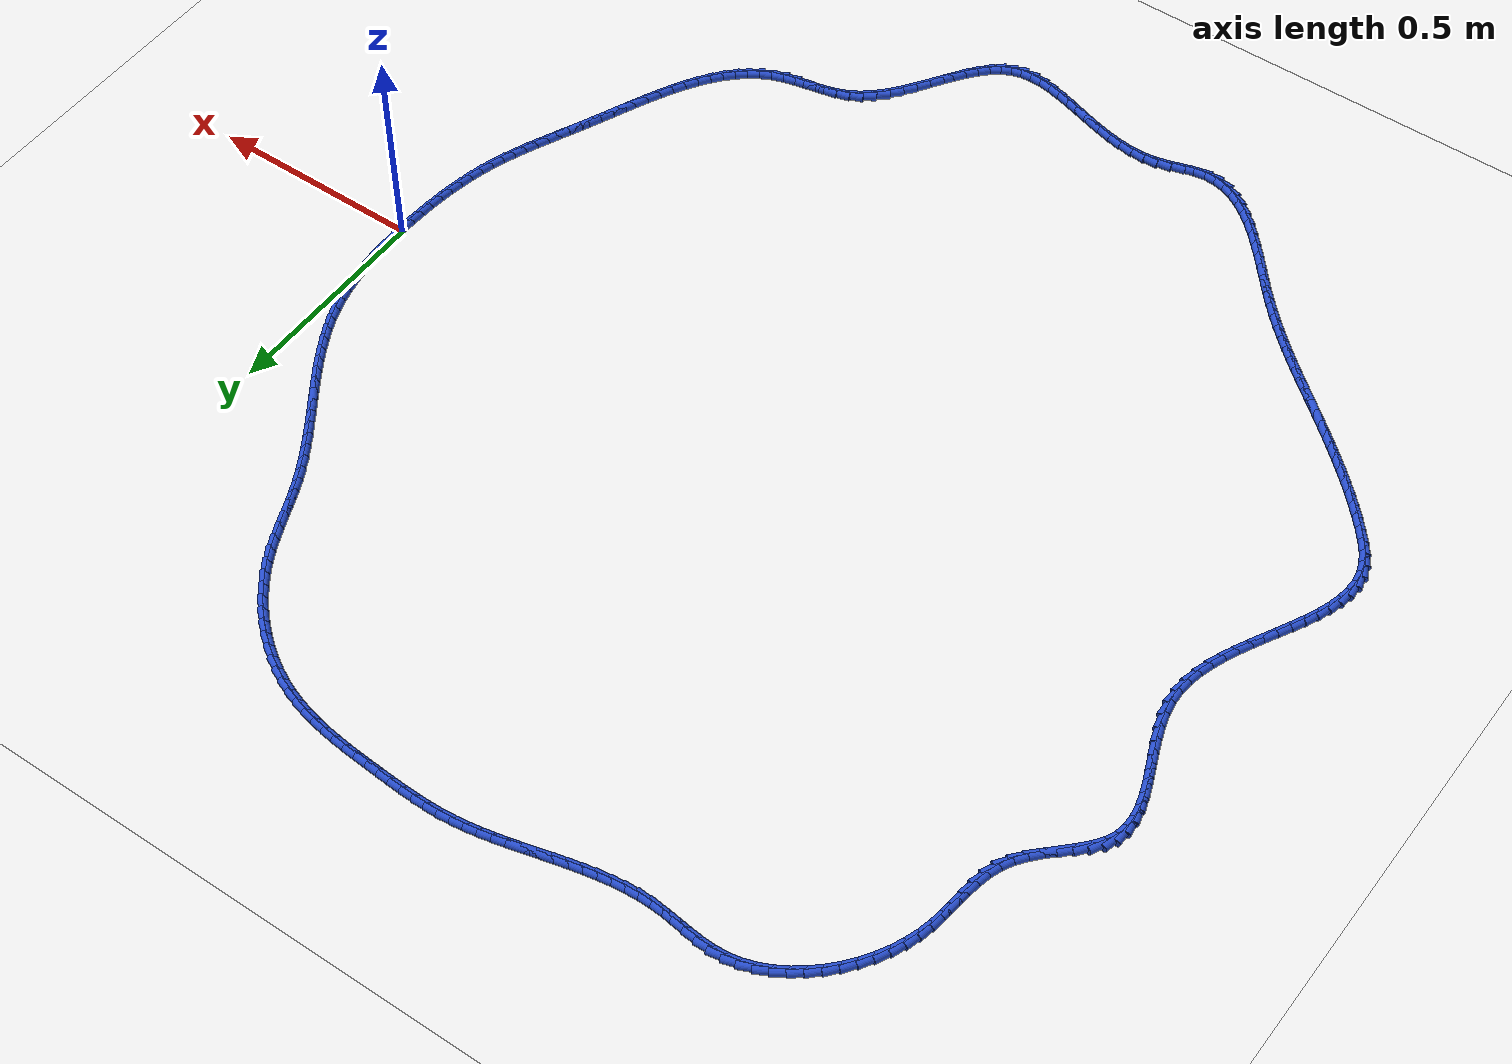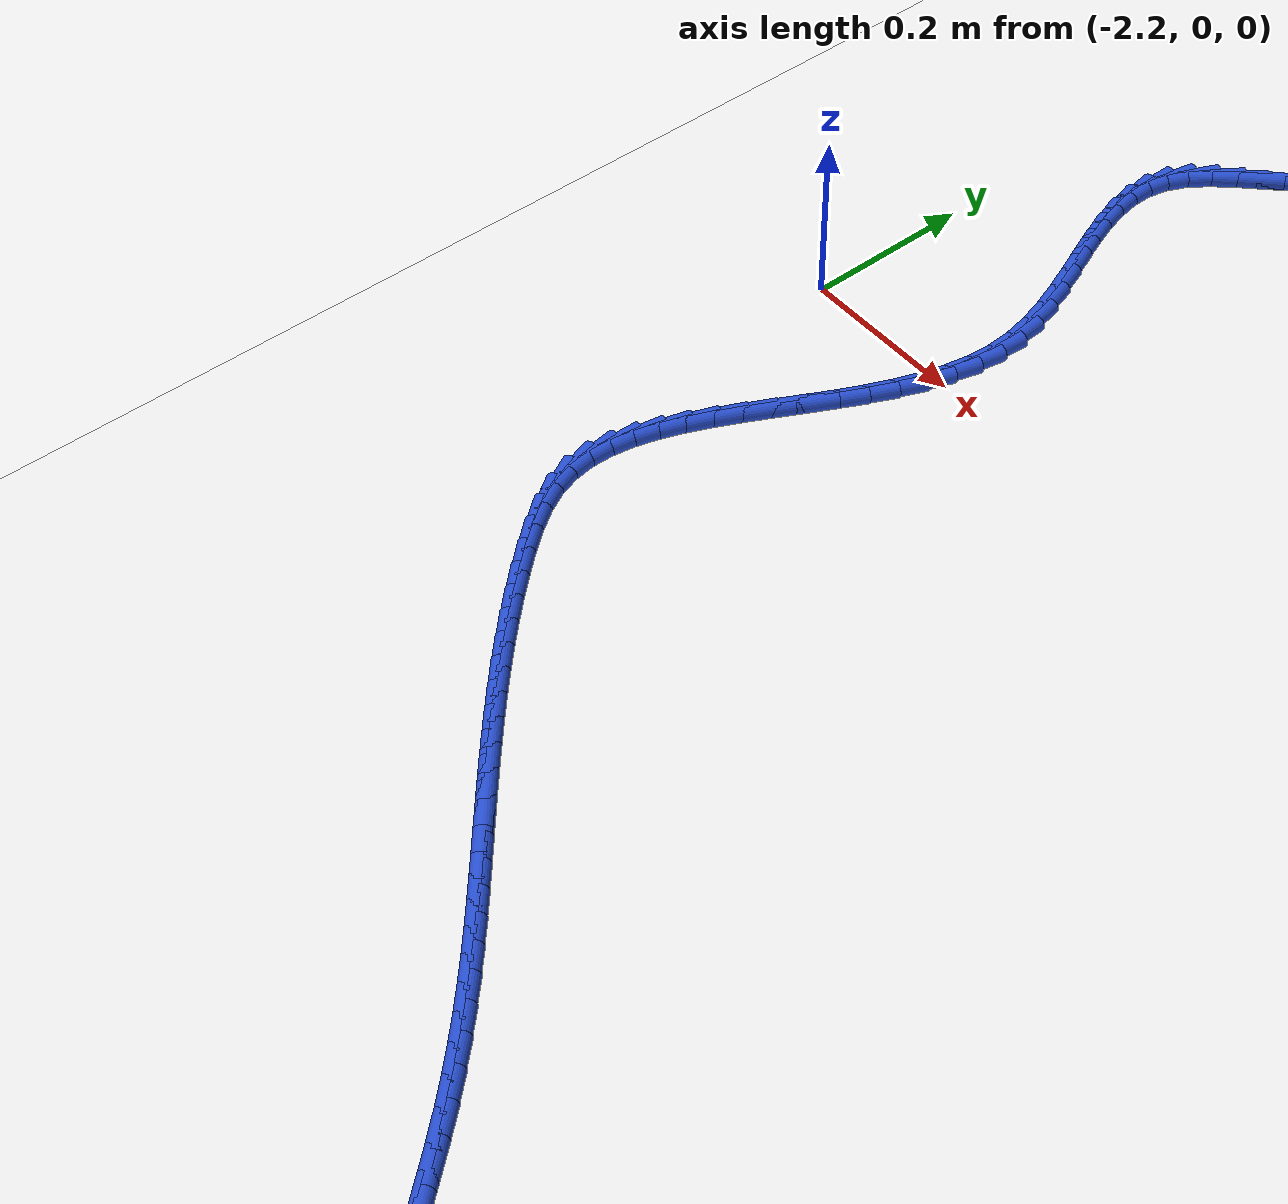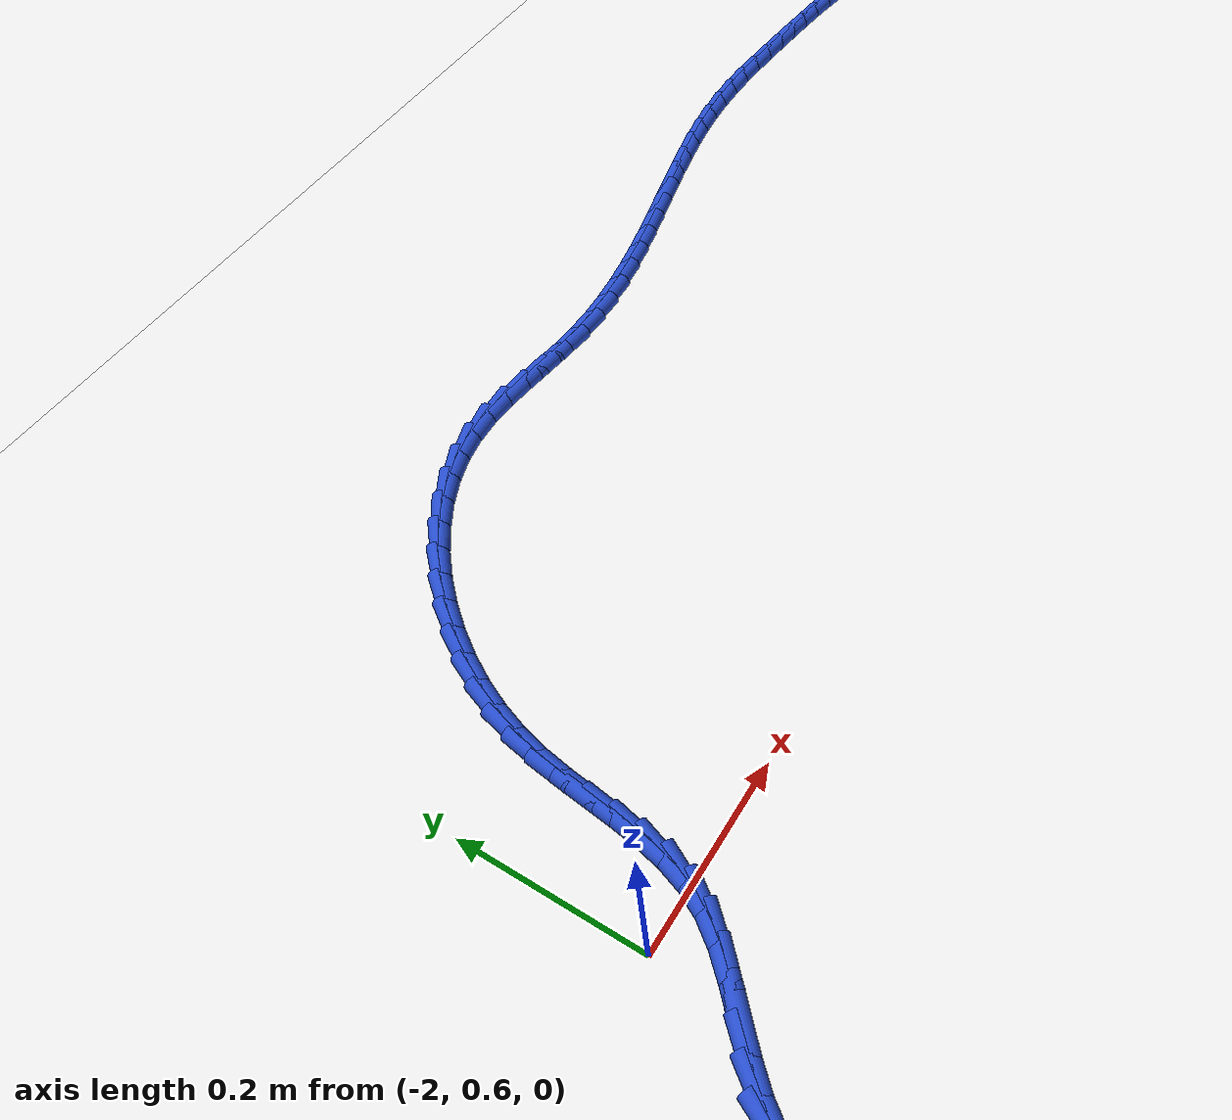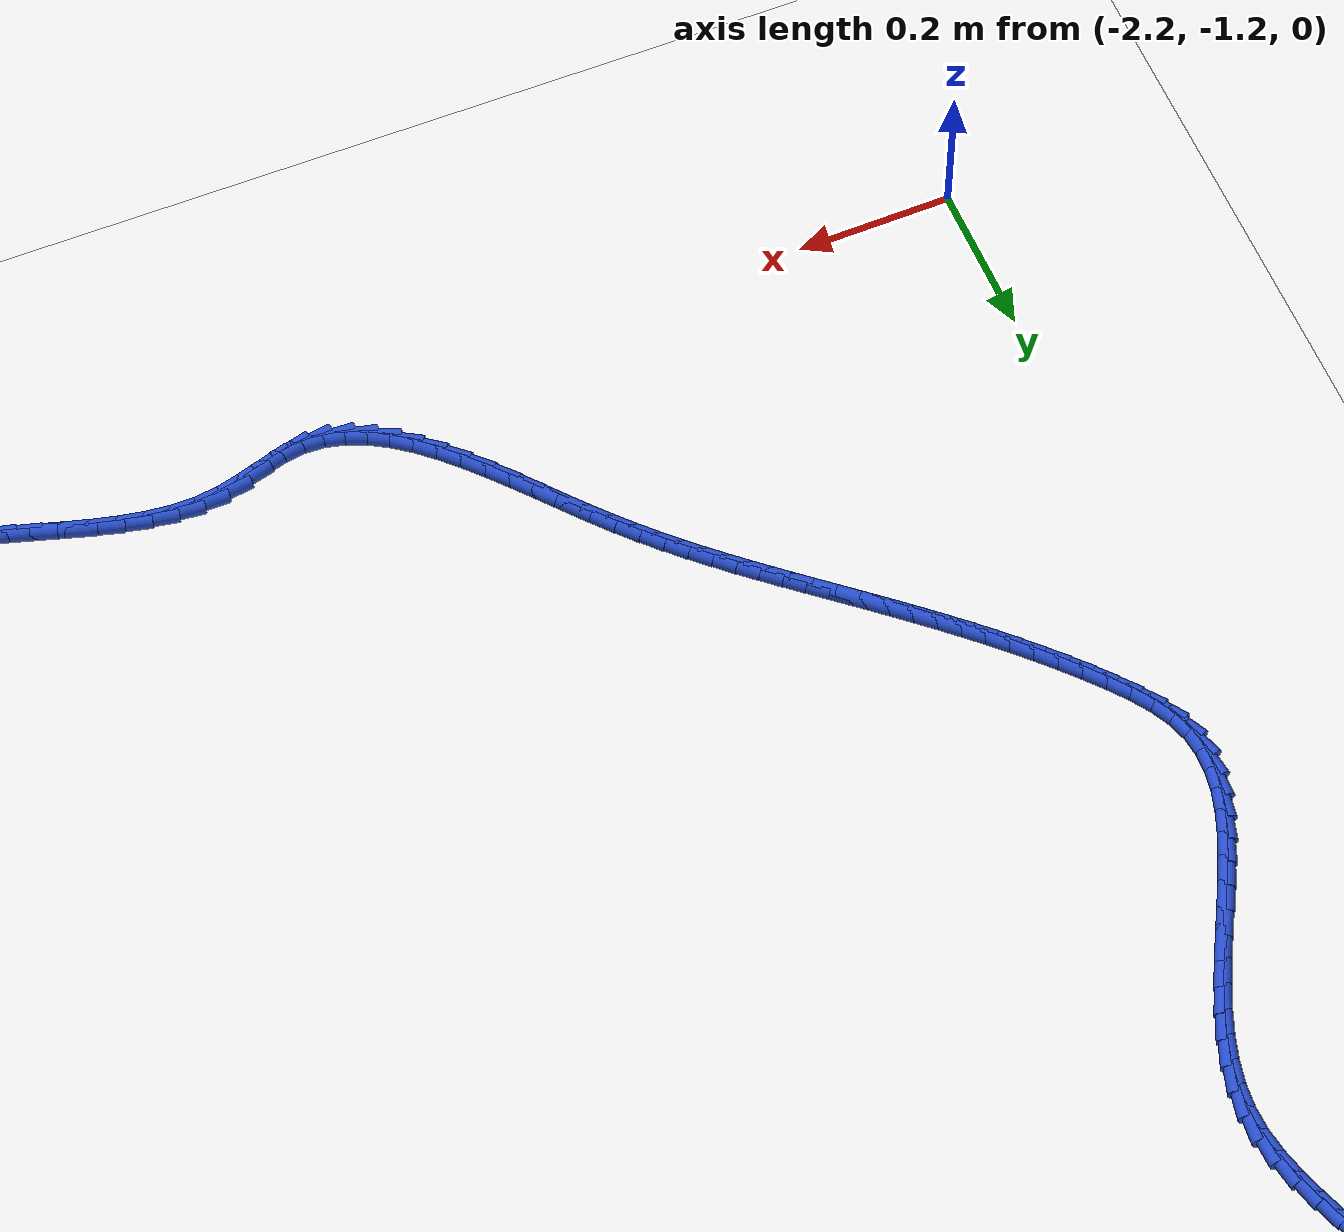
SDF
<sdf version="1.6">
 <world name="default">
  <light name="sun" type="directional">
   <pose>0 0 10 0 -0 0</pose>
   <diffuse>0.8 0.8 0.8 1</diffuse>
   <specular>0.2 0.2 0.2 1</specular>
   <attenuation>
    <range>1000</range>
    <constant>0.9</constant>
    <linear>0.01</linear>
    <quadratic>0.001</quadratic>
   </attenuation>
   <direction>-0.5 0.1 -0.9</direction>
  </light>
  <model name="ground_plane">
   <static>1</static>
   <link name="link">
    <collision name="collision">
     <geometry><plane><normal>0 0 1</normal><size>100 100</size></plane></geometry>
     <surface><friction><ode><mu>100</mu><mu2>50</mu2></ode></friction></surface>
    </collision>
    <visual name="visual">
     <cast_shadows>0</cast_shadows>
     <geometry><plane><normal>0 0 1</normal><size>100 100</size></plane></geometry>
     <material>
      <script><uri>file://media/materials/scripts/gazebo.material</uri><name>Gazebo/WhiteGlow</name></script>
     </material>
    </visual>
   </link>
  </model>
  <gravity>0 0 -9.8</gravity>
  <magnetic_field>6e-06 2.3e-05 -4.2e-05</magnetic_field>
  <atmosphere type="adiabatic"/>
  <physics name="default_physics" default="0" type="ode">
   <max_step_size>0.001</max_step_size>
   <real_time_factor>1</real_time_factor>
   <real_time_update_rate>1000</real_time_update_rate>
  </physics>
  <scene><ambient>0.4 0.4 0.4 1</ambient><background>0.7 0.7 0.7 1</background><shadows>1</shadows></scene>
  <spherical_coordinates>
   <surface_model>EARTH_WGS84</surface_model>
   <latitude_deg>0</latitude_deg>
   <longitude_deg>0</longitude_deg>
   <elevation>0</elevation>
   <heading_deg>0</heading_deg>
  </spherical_coordinates>
  <model name="line">
   <link name="link_0">
    <pose>-7.37257477290143e-18 -4.85722573273506e-17 0.01 0 1.57 1.5703176747545027</pose>
    <collision name="collision">
     <geometry><cylinder><radius>0.01</radius><length>0.08</length></cylinder></geometry>
    </collision>
    <visual name="visual">
     <material>
      <script><name>Gazebo/Blue</name><uri>file://media/materials/scripts/gazebo.material</uri></script>
     </material>
     <geometry><cylinder><radius>0.01</radius><length>0.08</length></cylinder></geometry>
    </visual>
   </link>
   <link name="link_1">
    <pose>1.4461063084984735e-05 0.030212055439494005 0.01 0 1.57 -1.5468161941087766</pose>
    <collision name="collision">
     <geometry><cylinder><radius>0.01</radius><length>0.08</length></cylinder></geometry>
    </collision>
    <visual name="visual">
     <material>
      <script><name>Gazebo/Blue</name><uri>file://media/materials/scripts/gazebo.material</uri></script>
     </material>
     <geometry><cylinder><radius>0.01</radius><length>0.08</length></cylinder></geometry>
    </visual>
   </link>
   <link name="link_2">
    <pose>-0.0007090973743195369 0.06037951732319605 0.01 0 1.57 -1.518462994660471</pose>
    <collision name="collision">
     <geometry><cylinder><radius>0.01</radius><length>0.08</length></cylinder></geometry>
    </collision>
    <visual name="visual">
     <material>
      <script><name>Gazebo/Blue</name><uri>file://media/materials/scripts/gazebo.material</uri></script>
     </material>
     <geometry><cylinder><radius>0.01</radius><length>0.08</length></cylinder></geometry>
    </visual>
   </link>
   <link name="link_3">
    <pose>-0.002282989804969906 0.09042643497516462 0.01 0 1.57 -1.4860249316204777</pose>
    <collision name="collision">
     <geometry><cylinder><radius>0.01</radius><length>0.08</length></cylinder></geometry>
    </collision>
    <visual name="visual">
     <material>
      <script><name>Gazebo/Blue</name><uri>file://media/materials/scripts/gazebo.material</uri></script>
     </material>
     <geometry><cylinder><radius>0.01</radius><length>0.08</length></cylinder></geometry>
    </visual>
   </link>
   <link name="link_4">
    <pose>-0.004819530721622448 0.1202768577194582 0.01 0 1.57 -1.4492966331668435</pose>
    <collision name="collision">
     <geometry><cylinder><radius>0.01</radius><length>0.08</length></cylinder></geometry>
    </collision>
    <visual name="visual">
     <material>
      <script><name>Gazebo/Blue</name><uri>file://media/materials/scripts/gazebo.material</uri></script>
     </material>
     <geometry><cylinder><radius>0.01</radius><length>0.08</length></cylinder></geometry>
    </visual>
   </link>
   <link name="link_5">
    <pose>-0.008431034617033494 0.1498548348801353 0.01 0 1.57 -1.4080724517758658</pose>
    <collision name="collision">
     <geometry><cylinder><radius>0.01</radius><length>0.08</length></cylinder></geometry>
    </collision>
    <visual name="visual">
     <material>
      <script><name>Gazebo/Blue</name><uri>file://media/materials/scripts/gazebo.material</uri></script>
     </material>
     <geometry><cylinder><radius>0.01</radius><length>0.08</length></cylinder></geometry>
    </visual>
   </link>
   <link name="link_6">
    <pose>-0.013229815983959378 0.17908441578125434 0.01 0 1.57 -1.3621663498640866</pose>
    <collision name="collision">
     <geometry><cylinder><radius>0.01</radius><length>0.08</length></cylinder></geometry>
    </collision>
    <visual name="visual">
     <material>
      <script><name>Gazebo/Blue</name><uri>file://media/materials/scripts/gazebo.material</uri></script>
     </material>
     <geometry><cylinder><radius>0.01</radius><length>0.08</length></cylinder></geometry>
    </visual>
   </link>
   <link name="link_7">
    <pose>-0.01932818931515642 0.20788964974687382 0.01 0 1.57 -1.3114379505265983</pose>
    <collision name="collision">
     <geometry><cylinder><radius>0.01</radius><length>0.08</length></cylinder></geometry>
    </collision>
    <visual name="visual">
     <material>
      <script><name>Gazebo/Blue</name><uri>file://media/materials/scripts/gazebo.material</uri></script>
     </material>
     <geometry><cylinder><radius>0.01</radius><length>0.08</length></cylinder></geometry>
    </visual>
   </link>
   <link name="link_8">
    <pose>-0.026838469103380953 0.2361945861010522 0.01 0 1.57 -1.2558365321164362</pose>
    <collision name="collision">
     <geometry><cylinder><radius>0.01</radius><length>0.08</length></cylinder></geometry>
    </collision>
    <visual name="visual">
     <material>
      <script><name>Gazebo/Blue</name><uri>file://media/materials/scripts/gazebo.material</uri></script>
     </material>
     <geometry><cylinder><radius>0.01</radius><length>0.08</length></cylinder></geometry>
    </visual>
   </link>
   <link name="link_9">
    <pose>-0.03587266493122443 0.26392343205464086 0.01 0 1.57 -1.1984196080494318</pose>
    <collision name="collision">
     <geometry><cylinder><radius>0.01</radius><length>0.08</length></cylinder></geometry>
    </collision>
    <visual name="visual">
     <material>
      <script><name>Gazebo/Blue</name><uri>file://media/materials/scripts/gazebo.material</uri></script>
     </material>
     <geometry><cylinder><radius>0.01</radius><length>0.08</length></cylinder></geometry>
    </visual>
   </link>
   <link name="link_10">
    <pose>-0.04646471582685968 0.2910408208550086 0.01 0 1.57 -1.1464235233692137</pose>
    <collision name="collision">
     <geometry><cylinder><radius>0.01</radius><length>0.08</length></cylinder></geometry>
    </collision>
    <visual name="visual">
     <material>
      <script><name>Gazebo/Blue</name><uri>file://media/materials/scripts/gazebo.material</uri></script>
     </material>
     <geometry><cylinder><radius>0.01</radius><length>0.08</length></cylinder></geometry>
    </visual>
   </link>
   <link name="link_11">
    <pose>-0.05846726643262977 0.31760526254489796 0.01 0 1.57 -1.101082894614376</pose>
    <collision name="collision">
     <geometry><cylinder><radius>0.01</radius><length>0.08</length></cylinder></geometry>
    </collision>
    <visual name="visual">
     <material>
      <script><name>Gazebo/Blue</name><uri>file://media/materials/scripts/gazebo.material</uri></script>
     </material>
     <geometry><cylinder><radius>0.01</radius><length>0.08</length></cylinder></geometry>
    </visual>
   </link>
   <link name="link_12">
    <pose>-0.0717072901378438 0.3436885601047071 0.01 0 1.57 -1.0624735519073758</pose>
    <collision name="collision">
     <geometry><cylinder><radius>0.01</radius><length>0.08</length></cylinder></geometry>
    </collision>
    <visual name="visual">
     <material>
      <script><name>Gazebo/Blue</name><uri>file://media/materials/scripts/gazebo.material</uri></script>
     </material>
     <geometry><cylinder><radius>0.01</radius><length>0.08</length></cylinder></geometry>
    </visual>
   </link>
   <link name="link_13">
    <pose>-0.08601176033181075 0.36936251651483404 0.01 0 1.57 -1.030549836354013</pose>
    <collision name="collision">
     <geometry><cylinder><radius>0.01</radius><length>0.08</length></cylinder></geometry>
    </collision>
    <visual name="visual">
     <material>
      <script><name>Gazebo/Blue</name><uri>file://media/materials/scripts/gazebo.material</uri></script>
     </material>
     <geometry><cylinder><radius>0.01</radius><length>0.08</length></cylinder></geometry>
    </visual>
   </link>
   <link name="link_14">
    <pose>-0.1012076504038397 0.3946989347556767 0.01 0 1.57 -1.0051975066920322</pose>
    <collision name="collision">
     <geometry><cylinder><radius>0.01</radius><length>0.08</length></cylinder></geometry>
    </collision>
    <visual name="visual">
     <material>
      <script><name>Gazebo/Blue</name><uri>file://media/materials/scripts/gazebo.material</uri></script>
     </material>
     <geometry><cylinder><radius>0.01</radius><length>0.08</length></cylinder></geometry>
    </visual>
   </link>
   <link name="link_15">
    <pose>-0.11712193374323963 0.4197696178076331 0.01 0 1.57 -0.9862763057004852</pose>
    <collision name="collision">
     <geometry><cylinder><radius>0.01</radius><length>0.08</length></cylinder></geometry>
    </collision>
    <visual name="visual">
     <material>
      <script><name>Gazebo/Blue</name><uri>file://media/materials/scripts/gazebo.material</uri></script>
     </material>
     <geometry><cylinder><radius>0.01</radius><length>0.08</length></cylinder></geometry>
    </visual>
   </link>
   <link name="link_16">
    <pose>-0.13358158373931966 0.4446463686511013 0.01 0 1.57 -0.9736515097091859</pose>
    <collision name="collision">
     <geometry><cylinder><radius>0.01</radius><length>0.08</length></cylinder></geometry>
    </collision>
    <visual name="visual">
     <material>
      <script><name>Gazebo/Blue</name><uri>file://media/materials/scripts/gazebo.material</uri></script>
     </material>
     <geometry><cylinder><radius>0.01</radius><length>0.08</length></cylinder></geometry>
    </visual>
   </link>
   <link name="link_17">
    <pose>-0.15041357378138878 0.4694009902664794 0.01 0 1.57 -0.9672154872259042</pose>
    <collision name="collision">
     <geometry><cylinder><radius>0.01</radius><length>0.08</length></cylinder></geometry>
    </collision>
    <visual name="visual">
     <material>
      <script><name>Gazebo/Blue</name><uri>file://media/materials/scripts/gazebo.material</uri></script>
     </material>
     <geometry><cylinder><radius>0.01</radius><length>0.08</length></cylinder></geometry>
    </visual>
   </link>
   <link name="link_18">
    <pose>-0.167444877258756 0.49410528563416545 0.01 0 1.57 -0.9669008236131983</pose>
    <collision name="collision">
     <geometry><cylinder><radius>0.01</radius><length>0.08</length></cylinder></geometry>
    </collision>
    <visual name="visual">
     <material>
      <script><name>Gazebo/Blue</name><uri>file://media/materials/scripts/gazebo.material</uri></script>
     </material>
     <geometry><cylinder><radius>0.01</radius><length>0.08</length></cylinder></geometry>
    </visual>
   </link>
   <link name="link_19">
    <pose>-0.18450246756073044 0.5188310577345571 0.01 0 1.57 -0.9726863884717935</pose>
    <collision name="collision">
     <geometry><cylinder><radius>0.01</radius><length>0.08</length></cylinder></geometry>
    </collision>
    <visual name="visual">
     <material>
      <script><name>Gazebo/Blue</name><uri>file://media/materials/scripts/gazebo.material</uri></script>
     </material>
     <geometry><cylinder><radius>0.01</radius><length>0.08</length></cylinder></geometry>
    </visual>
   </link>
   <link name="link_20">
    <pose>-0.20141331807662105 0.5436501095480528 0.01 0 1.57 -0.984597183898682</pose>
    <collision name="collision">
     <geometry><cylinder><radius>0.01</radius><length>0.08</length></cylinder></geometry>
    </collision>
    <visual name="visual">
     <material>
      <script><name>Gazebo/Blue</name><uri>file://media/materials/scripts/gazebo.material</uri></script>
     </material>
     <geometry><cylinder><radius>0.01</radius><length>0.08</length></cylinder></geometry>
    </visual>
   </link>
   <link name="link_21">
    <pose>-0.21800440219573697 0.5686342440550504 0.01 0 1.57 -1.0026981416675862</pose>
    <collision name="collision">
     <geometry><cylinder><radius>0.01</radius><length>0.08</length></cylinder></geometry>
    </collision>
    <visual name="visual">
     <material>
      <script><name>Gazebo/Blue</name><uri>file://media/materials/scripts/gazebo.material</uri></script>
     </material>
     <geometry><cylinder><radius>0.01</radius><length>0.08</length></cylinder></geometry>
    </visual>
   </link>
   <link name="link_22">
    <pose>-0.23410269330738717 0.5938552642359478 0.01 0 1.57 -1.0270813841281645</pose>
    <collision name="collision">
     <geometry><cylinder><radius>0.01</radius><length>0.08</length></cylinder></geometry>
    </collision>
    <visual name="visual">
     <material>
      <script><name>Gazebo/Blue</name><uri>file://media/materials/scripts/gazebo.material</uri></script>
     </material>
     <geometry><cylinder><radius>0.01</radius><length>0.08</length></cylinder></geometry>
    </visual>
   </link>
   <link name="link_23">
    <pose>-0.24953516480088064 0.6193849730711432 0.01 0 1.57 -1.0578459639371918</pose>
    <collision name="collision">
     <geometry><cylinder><radius>0.01</radius><length>0.08</length></cylinder></geometry>
    </collision>
    <visual name="visual">
     <material>
      <script><name>Gazebo/Blue</name><uri>file://media/materials/scripts/gazebo.material</uri></script>
     </material>
     <geometry><cylinder><radius>0.01</radius><length>0.08</length></cylinder></geometry>
    </visual>
   </link>
   <link name="link_24">
    <pose>-0.2641287900655266 0.6452951735410347 0.01 0 1.57 -1.095064450970841</pose>
    <collision name="collision">
     <geometry><cylinder><radius>0.01</radius><length>0.08</length></cylinder></geometry>
    </collision>
    <visual name="visual">
     <material>
      <script><name>Gazebo/Blue</name><uri>file://media/materials/scripts/gazebo.material</uri></script>
     </material>
     <geometry><cylinder><radius>0.01</radius><length>0.08</length></cylinder></geometry>
    </visual>
   </link>
   <link name="link_25">
    <pose>-0.2777106649210383 0.6716576156773398 0.01 0 1.57 -1.1339365389686895</pose>
    <collision name="collision">
     <geometry><cylinder><radius>0.01</radius><length>0.08</length></cylinder></geometry>
    </collision>
    <visual name="visual">
     <material>
      <script><name>Gazebo/Blue</name><uri>file://media/materials/scripts/gazebo.material</uri></script>
     </material>
     <geometry><cylinder><radius>0.01</radius><length>0.08</length></cylinder></geometry>
    </visual>
   </link>
   <link name="link_26">
    <pose>-0.29023883915279275 0.6984874145633994 0.01 0 1.57 -1.1603927286373734</pose>
    <collision name="collision">
     <geometry><cylinder><radius>0.01</radius><length>0.08</length></cylinder></geometry>
    </collision>
    <visual name="visual">
     <material>
      <script><name>Gazebo/Blue</name><uri>file://media/materials/scripts/gazebo.material</uri></script>
     </material>
     <geometry><cylinder><radius>0.01</radius><length>0.08</length></cylinder></geometry>
    </visual>
   </link>
   <link name="link_27">
    <pose>-0.30205122987205557 0.7256354003272797 0.01 0 1.57 -1.1718510174751262</pose>
    <collision name="collision">
     <geometry><cylinder><radius>0.01</radius><length>0.08</length></cylinder></geometry>
    </collision>
    <visual name="visual">
     <material>
      <script><name>Gazebo/Blue</name><uri>file://media/materials/scripts/gazebo.material</uri></script>
     </material>
     <geometry><cylinder><radius>0.01</radius><length>0.08</length></cylinder></geometry>
    </visual>
   </link>
   <link name="link_28">
    <pose>-0.313554241404602 0.7529227837583837 0.01 0 1.57 -1.1683153209630228</pose>
    <collision name="collision">
     <geometry><cylinder><radius>0.01</radius><length>0.08</length></cylinder></geometry>
    </collision>
    <visual name="visual">
     <material>
      <script><name>Gazebo/Blue</name><uri>file://media/materials/scripts/gazebo.material</uri></script>
     </material>
     <geometry><cylinder><radius>0.01</radius><length>0.08</length></cylinder></geometry>
    </visual>
   </link>
   <link name="link_29">
    <pose>-0.32515427807620667 0.7801707756461143 0.01 0 1.57 -1.1497883213732725</pose>
    <collision name="collision">
     <geometry><cylinder><radius>0.01</radius><length>0.08</length></cylinder></geometry>
    </collision>
    <visual name="visual">
     <material>
      <script><name>Gazebo/Blue</name><uri>file://media/materials/scripts/gazebo.material</uri></script>
     </material>
     <geometry><cylinder><radius>0.01</radius><length>0.08</length></cylinder></geometry>
    </visual>
   </link>
   <link name="link_30">
    <pose>-0.3372577442126451 0.8072005867798756 0.01 0 1.57 -1.1162952735850844</pose>
    <collision name="collision">
     <geometry><cylinder><radius>0.01</radius><length>0.08</length></cylinder></geometry>
    </collision>
    <visual name="visual">
     <material>
      <script><name>Gazebo/Blue</name><uri>file://media/materials/scripts/gazebo.material</uri></script>
     </material>
     <geometry><cylinder><radius>0.01</radius><length>0.08</length></cylinder></geometry>
    </visual>
   </link>
   <link name="link_31">
    <pose>-0.35027104413969185 0.8338334279490695 0.01 0 1.57 -1.0680078343342836</pose>
    <collision name="collision">
     <geometry><cylinder><radius>0.01</radius><length>0.08</length></cylinder></geometry>
    </collision>
    <visual name="visual">
     <material>
      <script><name>Gazebo/Blue</name><uri>file://media/materials/scripts/gazebo.material</uri></script>
     </material>
     <geometry><cylinder><radius>0.01</radius><length>0.08</length></cylinder></geometry>
    </visual>
   </link>
   <link name="link_32">
    <pose>-0.3646005821831223 0.8598905099431002 0.01 0 1.57 -1.0080423370805933</pose>
    <collision name="collision">
     <geometry><cylinder><radius>0.01</radius><length>0.08</length></cylinder></geometry>
    </collision>
    <visual name="visual">
     <material>
      <script><name>Gazebo/Blue</name><uri>file://media/materials/scripts/gazebo.material</uri></script>
     </material>
     <geometry><cylinder><radius>0.01</radius><length>0.08</length></cylinder></geometry>
    </visual>
   </link>
   <link name="link_33">
    <pose>-0.38056796587997116 0.8852037142345754 0.01 0 1.57 -0.9471541938286397</pose>
    <collision name="collision">
     <geometry><cylinder><radius>0.01</radius><length>0.08</length></cylinder></geometry>
    </collision>
    <visual name="visual">
     <material>
      <script><name>Gazebo/Blue</name><uri>file://media/materials/scripts/gazebo.material</uri></script>
     </material>
     <geometry><cylinder><radius>0.01</radius><length>0.08</length></cylinder></geometry>
    </visual>
   </link>
   <link name="link_34">
    <pose>-0.3981536142375855 0.9096478568785027 0.01 0 1.57 -0.8875377673563339</pose>
    <collision name="collision">
     <geometry><cylinder><radius>0.01</radius><length>0.08</length></cylinder></geometry>
    </collision>
    <visual name="visual">
     <material>
      <script><name>Gazebo/Blue</name><uri>file://media/materials/scripts/gazebo.material</uri></script>
     </material>
     <geometry><cylinder><radius>0.01</radius><length>0.08</length></cylinder></geometry>
    </visual>
   </link>
   <link name="link_35">
    <pose>-0.417252145838474 0.9331085509089488 0.01 0 1.57 -0.828685149573534</pose>
    <collision name="collision">
     <geometry><cylinder><radius>0.01</radius><length>0.08</length></cylinder></geometry>
    </collision>
    <visual name="visual">
     <material>
      <script><name>Gazebo/Blue</name><uri>file://media/materials/scripts/gazebo.material</uri></script>
     </material>
     <geometry><cylinder><radius>0.01</radius><length>0.08</length></cylinder></geometry>
    </visual>
   </link>
   <link name="link_36">
    <pose>-0.4377581792645012 0.9554714093600614 0.01 0 1.57 -0.7700935751304727</pose>
    <collision name="collision">
     <geometry><cylinder><radius>0.01</radius><length>0.08</length></cylinder></geometry>
    </collision>
    <visual name="visual">
     <material>
      <script><name>Gazebo/Blue</name><uri>file://media/materials/scripts/gazebo.material</uri></script>
     </material>
     <geometry><cylinder><radius>0.01</radius><length>0.08</length></cylinder></geometry>
    </visual>
   </link>
   <link name="link_37">
    <pose>-0.4595663330975323 0.976622045265988 0.01 0 1.57 -0.7112651403275346</pose>
    <collision name="collision">
     <geometry><cylinder><radius>0.01</radius><length>0.08</length></cylinder></geometry>
    </collision>
    <visual name="visual">
     <material>
      <script><name>Gazebo/Blue</name><uri>file://media/materials/scripts/gazebo.material</uri></script>
     </material>
     <geometry><cylinder><radius>0.01</radius><length>0.08</length></cylinder></geometry>
    </visual>
   </link>
   <link name="link_38">
    <pose>-0.4825712259194319 0.9964460716608758 0.01 0 1.57 -0.6517061310487865</pose>
    <collision name="collision">
     <geometry><cylinder><radius>0.01</radius><length>0.08</length></cylinder></geometry>
    </collision>
    <visual name="visual">
     <material>
      <script><name>Gazebo/Blue</name><uri>file://media/materials/scripts/gazebo.material</uri></script>
     </material>
     <geometry><cylinder><radius>0.01</radius><length>0.08</length></cylinder></geometry>
    </visual>
   </link>
   <link name="link_39">
    <pose>-0.5066674763120652 1.0148291015788733 0.01 0 1.57 -0.5909271183176295</pose>
    <collision name="collision">
     <geometry><cylinder><radius>0.01</radius><length>0.08</length></cylinder></geometry>
    </collision>
    <visual name="visual">
     <material>
      <script><name>Gazebo/Blue</name><uri>file://media/materials/scripts/gazebo.material</uri></script>
     </material>
     <geometry><cylinder><radius>0.01</radius><length>0.08</length></cylinder></geometry>
    </visual>
   </link>
   <link name="link_40">
    <pose>-0.5317497028572966 1.0316567480541274 0.01 0 1.57 -0.528444999137504</pose>
    <collision name="collision">
     <geometry><cylinder><radius>0.01</radius><length>0.08</length></cylinder></geometry>
    </collision>
    <visual name="visual">
     <material>
      <script><name>Gazebo/Blue</name><uri>file://media/materials/scripts/gazebo.material</uri></script>
     </material>
     <geometry><cylinder><radius>0.01</radius><length>0.08</length></cylinder></geometry>
    </visual>
   </link>
   <link name="link_41">
    <pose>-0.5577125241369915 1.0468146241207859 0.01 0 1.57 -0.46378826447084043</pose>
    <collision name="collision">
     <geometry><cylinder><radius>0.01</radius><length>0.08</length></cylinder></geometry>
    </collision>
    <visual name="visual">
     <material>
      <script><name>Gazebo/Blue</name><uri>file://media/materials/scripts/gazebo.material</uri></script>
     </material>
     <geometry><cylinder><radius>0.01</radius><length>0.08</length></cylinder></geometry>
    </visual>
   </link>
   <link name="link_42">
    <pose>-0.5844505587330143 1.0601883428129966 0.01 0 1.57 -0.3965112653725849</pose>
    <collision name="collision">
     <geometry><cylinder><radius>0.01</radius><length>0.08</length></cylinder></geometry>
    </collision>
    <visual name="visual">
     <material>
      <script><name>Gazebo/Blue</name><uri>file://media/materials/scripts/gazebo.material</uri></script>
     </material>
     <geometry><cylinder><radius>0.01</radius><length>0.08</length></cylinder></geometry>
    </visual>
   </link>
   <link name="link_43">
    <pose>-0.6118584381919879 1.0716636628633203 0.01 0 1.57 -0.32879017214554823</pose>
    <collision name="collision">
     <geometry><cylinder><radius>0.01</radius><length>0.08</length></cylinder></geometry>
    </collision>
    <visual name="visual">
     <material>
      <script><name>Gazebo/Blue</name><uri>file://media/materials/scripts/gazebo.material</uri></script>
     </material>
     <geometry><cylinder><radius>0.01</radius><length>0.08</length></cylinder></geometry>
    </visual>
   </link>
   <link name="link_44">
    <pose>-0.6398382045268702 1.081209622093059 0.01 0 1.57 -0.267644319476524</pose>
    <collision name="collision">
     <geometry><cylinder><radius>0.01</radius><length>0.08</length></cylinder></geometry>
    </collision>
    <visual name="visual">
     <material>
      <script><name>Gazebo/Blue</name><uri>file://media/materials/scripts/gazebo.material</uri></script>
     </material>
     <geometry><cylinder><radius>0.01</radius><length>0.08</length></cylinder></geometry>
    </visual>
   </link>
   <link name="link_45">
    <pose>-0.6683116958283967 1.0890177273616286 0.01 0 1.57 -0.21464124068219143</pose>
    <collision name="collision">
     <geometry><cylinder><radius>0.01</radius><length>0.08</length></cylinder></geometry>
    </collision>
    <visual name="visual">
     <material>
      <script><name>Gazebo/Blue</name><uri>file://media/materials/scripts/gazebo.material</uri></script>
     </material>
     <geometry><cylinder><radius>0.01</radius><length>0.08</length></cylinder></geometry>
    </visual>
   </link>
   <link name="link_46">
    <pose>-0.6972040203780528 1.095316236050397 0.01 0 1.57 -0.16995232038957006</pose>
    <collision name="collision">
     <geometry><cylinder><radius>0.01</radius><length>0.08</length></cylinder></geometry>
    </collision>
    <visual name="visual">
     <material>
      <script><name>Gazebo/Blue</name><uri>file://media/materials/scripts/gazebo.material</uri></script>
     </material>
     <geometry><cylinder><radius>0.01</radius><length>0.08</length></cylinder></geometry>
    </visual>
   </link>
   <link name="link_47">
    <pose>-0.7264402864573243 1.100333405540731 0.01 0 1.57 -0.13355192131139942</pose>
    <collision name="collision">
     <geometry><cylinder><radius>0.01</radius><length>0.08</length></cylinder></geometry>
    </collision>
    <visual name="visual">
     <material>
      <script><name>Gazebo/Blue</name><uri>file://media/materials/scripts/gazebo.material</uri></script>
     </material>
     <geometry><cylinder><radius>0.01</radius><length>0.08</length></cylinder></geometry>
    </visual>
   </link>
   <link name="link_48">
    <pose>-0.7559456023476968 1.104297493213998 0.01 0 1.57 -0.10530993409976899</pose>
    <collision name="collision">
     <geometry><cylinder><radius>0.01</radius><length>0.08</length></cylinder></geometry>
    </collision>
    <visual name="visual">
     <material>
      <script><name>Gazebo/Blue</name><uri>file://media/materials/scripts/gazebo.material</uri></script>
     </material>
     <geometry><cylinder><radius>0.01</radius><length>0.08</length></cylinder></geometry>
    </visual>
   </link>
   <link name="link_49">
    <pose>-0.7856450763306565 1.1074367564515655 0.01 0 1.57 -0.08506596935890784</pose>
    <collision name="collision">
     <geometry><cylinder><radius>0.01</radius><length>0.08</length></cylinder></geometry>
    </collision>
    <visual name="visual">
     <material>
      <script><name>Gazebo/Blue</name><uri>file://media/materials/scripts/gazebo.material</uri></script>
     </material>
     <geometry><cylinder><radius>0.01</radius><length>0.08</length></cylinder></geometry>
    </visual>
   </link>
   <link name="link_50">
    <pose>-0.8154638166876889 1.1099794526348008 0.01 0 1.57 -0.07268351419006149</pose>
    <collision name="collision">
     <geometry><cylinder><radius>0.01</radius><length>0.08</length></cylinder></geometry>
    </collision>
    <visual name="visual">
     <material>
      <script><name>Gazebo/Blue</name><uri>file://media/materials/scripts/gazebo.material</uri></script>
     </material>
     <geometry><cylinder><radius>0.01</radius><length>0.08</length></cylinder></geometry>
    </visual>
   </link>
   <link name="link_51">
    <pose>-0.8453269317002794 1.1121538391450712 0.01 0 1.57 -0.0675079938536414</pose>
    <collision name="collision">
     <geometry><cylinder><radius>0.01</radius><length>0.08</length></cylinder></geometry>
    </collision>
    <visual name="visual">
     <material>
      <script><name>Gazebo/Blue</name><uri>file://media/materials/scripts/gazebo.material</uri></script>
     </material>
     <geometry><cylinder><radius>0.01</radius><length>0.08</length></cylinder></geometry>
    </visual>
   </link>
   <link name="link_52">
    <pose>-0.875162102999599 1.114171016951641 0.01 0 1.57 -0.061119635248923984</pose>
    <collision name="collision">
     <geometry><cylinder><radius>0.01</radius><length>0.08</length></cylinder></geometry>
    </collision>
    <visual name="visual">
     <material>
      <script><name>Gazebo/Blue</name><uri>file://media/materials/scripts/gazebo.material</uri></script>
     </material>
     <geometry><cylinder><radius>0.01</radius><length>0.08</length></cylinder></geometry>
    </visual>
   </link>
   <link name="link_53">
    <pose>-0.9049343801041758 1.1159929569196063 0.01 0 1.57 -0.047122426127282645</pose>
    <collision name="collision">
     <geometry><cylinder><radius>0.01</radius><length>0.08</length></cylinder></geometry>
    </collision>
    <visual name="visual">
     <material>
      <script><name>Gazebo/Blue</name><uri>file://media/materials/scripts/gazebo.material</uri></script>
     </material>
     <geometry><cylinder><radius>0.01</radius><length>0.08</length></cylinder></geometry>
    </visual>
   </link>
   <link name="link_54">
    <pose>-0.9346370077346836 1.1173936537092533 0.01 0 1.57 -0.025269866625905996</pose>
    <collision name="collision">
     <geometry><cylinder><radius>0.01</radius><length>0.08</length></cylinder></geometry>
    </collision>
    <visual name="visual">
     <material>
      <script><name>Gazebo/Blue</name><uri>file://media/materials/scripts/gazebo.material</uri></script>
     </material>
     <geometry><cylinder><radius>0.01</radius><length>0.08</length></cylinder></geometry>
    </visual>
   </link>
   <link name="link_55">
    <pose>-0.964263923680349 1.118142481322514 0.01 0 1.57 0.004524149824682729</pose>
    <collision name="collision">
     <geometry><cylinder><radius>0.01</radius><length>0.08</length></cylinder></geometry>
    </collision>
    <visual name="visual">
     <material>
      <script><name>Gazebo/Blue</name><uri>file://media/materials/scripts/gazebo.material</uri></script>
     </material>
     <geometry><cylinder><radius>0.01</radius><length>0.08</length></cylinder></geometry>
    </visual>
   </link>
   <link name="link_56">
    <pose>-0.9938090657303992 1.1180088137613207 0.01 0 1.57 0.042300033275450295</pose>
    <collision name="collision">
     <geometry><cylinder><radius>0.01</radius><length>0.08</length></cylinder></geometry>
    </collision>
    <visual name="visual">
     <material>
      <script><name>Gazebo/Blue</name><uri>file://media/materials/scripts/gazebo.material</uri></script>
     </material>
     <geometry><cylinder><radius>0.01</radius><length>0.08</length></cylinder></geometry>
    </visual>
   </link>
   <link name="link_57">
    <pose>-1.023266371674061 1.1167620250276051 0.01 0 1.57 0.08789325479259164</pose>
    <collision name="collision">
     <geometry><cylinder><radius>0.01</radius><length>0.08</length></cylinder></geometry>
    </collision>
    <visual name="visual">
     <material>
      <script><name>Gazebo/Blue</name><uri>file://media/materials/scripts/gazebo.material</uri></script>
     </material>
     <geometry><cylinder><radius>0.01</radius><length>0.08</length></cylinder></geometry>
    </visual>
   </link>
   <link name="link_58">
    <pose>-1.0526299182384042 1.1141745008455288 0.01 0 1.57 0.13507528991438397</pose>
    <collision name="collision">
     <geometry><cylinder><radius>0.01</radius><length>0.08</length></cylinder></geometry>
    </collision>
    <visual name="visual">
     <material>
      <script><name>Gazebo/Blue</name><uri>file://media/materials/scripts/gazebo.material</uri></script>
     </material>
     <geometry><cylinder><radius>0.01</radius><length>0.08</length></cylinder></geometry>
    </visual>
   </link>
   <link name="link_59">
    <pose>-1.081901980693283 1.1101963447810264 0.01 0 1.57 0.17443238515272955</pose>
    <collision name="collision">
     <geometry><cylinder><radius>0.01</radius><length>0.08</length></cylinder></geometry>
    </collision>
    <visual name="visual">
     <material>
      <script><name>Gazebo/Blue</name><uri>file://media/materials/scripts/gazebo.material</uri></script>
     </material>
     <geometry><cylinder><radius>0.01</radius><length>0.08</length></cylinder></geometry>
    </visual>
   </link>
   <link name="link_60">
    <pose>-1.1110974634827628 1.105051419974475 0.01 0 1.57 0.20522141441779013</pose>
    <collision name="collision">
     <geometry><cylinder><radius>0.01</radius><length>0.08</length></cylinder></geometry>
    </collision>
    <visual name="visual">
     <material>
      <script><name>Gazebo/Blue</name><uri>file://media/materials/scripts/gazebo.material</uri></script>
     </material>
     <geometry><cylinder><radius>0.01</radius><length>0.08</length></cylinder></geometry>
    </visual>
   </link>
   <link name="link_61">
    <pose>-1.1402323483003993 1.0989869408446247 0.01 0 1.57 0.22757157438810824</pose>
    <collision name="collision">
     <geometry><cylinder><radius>0.01</radius><length>0.08</length></cylinder></geometry>
    </collision>
    <visual name="visual">
     <material>
      <script><name>Gazebo/Blue</name><uri>file://media/materials/scripts/gazebo.material</uri></script>
     </material>
     <geometry><cylinder><radius>0.01</radius><length>0.08</length></cylinder></geometry>
    </visual>
   </link>
   <link name="link_62">
    <pose>-1.1693226168397495 1.0922501218102276 0.01 0 1.57 0.24162513084706339</pose>
    <collision name="collision">
     <geometry><cylinder><radius>0.01</radius><length>0.08</length></cylinder></geometry>
    </collision>
    <visual name="visual">
     <material>
      <script><name>Gazebo/Blue</name><uri>file://media/materials/scripts/gazebo.material</uri></script>
     </material>
     <geometry><cylinder><radius>0.01</radius><length>0.08</length></cylinder></geometry>
    </visual>
   </link>
   <link name="link_63">
    <pose>-1.1983842507943707 1.085088177290035 0.01 0 1.57 0.24749162441161918</pose>
    <collision name="collision">
     <geometry><cylinder><radius>0.01</radius><length>0.08</length></cylinder></geometry>
    </collision>
    <visual name="visual">
     <material>
      <script><name>Gazebo/Blue</name><uri>file://media/materials/scripts/gazebo.material</uri></script>
     </material>
     <geometry><cylinder><radius>0.01</radius><length>0.08</length></cylinder></geometry>
    </visual>
   </link>
   <link name="link_64">
    <pose>-1.227433231857819 1.077748321702798 0.01 0 1.57 0.24522080052676498</pose>
    <collision name="collision">
     <geometry><cylinder><radius>0.01</radius><length>0.08</length></cylinder></geometry>
    </collision>
    <visual name="visual">
     <material>
      <script><name>Gazebo/Blue</name><uri>file://media/materials/scripts/gazebo.material</uri></script>
     </material>
     <geometry><cylinder><radius>0.01</radius><length>0.08</length></cylinder></geometry>
    </visual>
   </link>
   <link name="link_65">
    <pose>-1.256485541723651 1.0704777694672685 0.01 0 1.57 0.23479176100697835</pose>
    <collision name="collision">
     <geometry><cylinder><radius>0.01</radius><length>0.08</length></cylinder></geometry>
    </collision>
    <visual name="visual">
     <material>
      <script><name>Gazebo/Blue</name><uri>file://media/materials/scripts/gazebo.material</uri></script>
     </material>
     <geometry><cylinder><radius>0.01</radius><length>0.08</length></cylinder></geometry>
    </visual>
   </link>
   <link name="link_66">
    <pose>-1.2855571620854238 1.0635237350021969 0.01 0 1.57 0.2161170935478966</pose>
    <collision name="collision">
     <geometry><cylinder><radius>0.01</radius><length>0.08</length></cylinder></geometry>
    </collision>
    <visual name="visual">
     <material>
      <script><name>Gazebo/Blue</name><uri>file://media/materials/scripts/gazebo.material</uri></script>
     </material>
     <geometry><cylinder><radius>0.01</radius><length>0.08</length></cylinder></geometry>
    </visual>
   </link>
   <link name="link_67">
    <pose>-1.3146640746366942 1.0571334327263355 0.01 0 1.57 0.18906249187936325</pose>
    <collision name="collision">
     <geometry><cylinder><radius>0.01</radius><length>0.08</length></cylinder></geometry>
    </collision>
    <visual name="visual">
     <material>
      <script><name>Gazebo/Blue</name><uri>file://media/materials/scripts/gazebo.material</uri></script>
     </material>
     <geometry><cylinder><radius>0.01</radius><length>0.08</length></cylinder></geometry>
    </visual>
   </link>
   <link name="link_68">
    <pose>-1.3438222610710182 1.0515540770584348 0.01 0 1.57 0.15348395219990973</pose>
    <collision name="collision">
     <geometry><cylinder><radius>0.01</radius><length>0.08</length></cylinder></geometry>
    </collision>
    <visual name="visual">
     <material>
      <script><name>Gazebo/Blue</name><uri>file://media/materials/scripts/gazebo.material</uri></script>
     </material>
     <geometry><cylinder><radius>0.01</radius><length>0.08</length></cylinder></geometry>
    </visual>
   </link>
   <link name="link_69">
    <pose>-1.373047703081953 1.0470328824172468 0.01 0 1.57 0.1092852563280532</pose>
    <collision name="collision">
     <geometry><cylinder><radius>0.01</radius><length>0.08</length></cylinder></geometry>
    </collision>
    <visual name="visual">
     <material>
      <script><name>Gazebo/Blue</name><uri>file://media/materials/scripts/gazebo.material</uri></script>
     </material>
     <geometry><cylinder><radius>0.01</radius><length>0.08</length></cylinder></geometry>
    </visual>
   </link>
   <link name="link_70">
    <pose>-1.4023563823630563 1.0438170632215225 0.01 0 1.57 0.05649704414639845</pose>
    <collision name="collision">
     <geometry><cylinder><radius>0.01</radius><length>0.08</length></cylinder></geometry>
    </collision>
    <visual name="visual">
     <material>
      <script><name>Gazebo/Blue</name><uri>file://media/materials/scripts/gazebo.material</uri></script>
     </material>
     <geometry><cylinder><radius>0.01</radius><length>0.08</length></cylinder></geometry>
    </visual>
   </link>
   <link name="link_71">
    <pose>-1.431764280607883 1.0421538338900131 0.01 0 1.57 -0.00462600412232268</pose>
    <collision name="collision">
     <geometry><cylinder><radius>0.01</radius><length>0.08</length></cylinder></geometry>
    </collision>
    <visual name="visual">
     <material>
      <script><name>Gazebo/Blue</name><uri>file://media/materials/scripts/gazebo.material</uri></script>
     </material>
     <geometry><cylinder><radius>0.01</radius><length>0.08</length></cylinder></geometry>
    </visual>
   </link>
   <link name="link_72">
    <pose>-1.4612873795099905 1.0422904088414702 0.01 0 1.57 -0.07126255474512719</pose>
    <collision name="collision">
     <geometry><cylinder><radius>0.01</radius><length>0.08</length></cylinder></geometry>
    </collision>
    <visual name="visual">
     <material>
      <script><name>Gazebo/Blue</name><uri>file://media/materials/scripts/gazebo.material</uri></script>
     </material>
     <geometry><cylinder><radius>0.01</radius><length>0.08</length></cylinder></geometry>
    </visual>
   </link>
   <link name="link_73">
    <pose>-1.4909364174710387 1.0444068589384972 0.01 0 1.57 -0.11735615497983054</pose>
    <collision name="collision">
     <geometry><cylinder><radius>0.01</radius><length>0.08</length></cylinder></geometry>
    </collision>
    <visual name="visual">
     <material>
      <script><name>Gazebo/Blue</name><uri>file://media/materials/scripts/gazebo.material</uri></script>
     </material>
     <geometry><cylinder><radius>0.01</radius><length>0.08</length></cylinder></geometry>
    </visual>
   </link>
   <link name="link_74">
    <pose>-1.520661860188151 1.04791142623842 0.01 0 1.57 -0.12743091473736504</pose>
    <collision name="collision">
     <geometry><cylinder><radius>0.01</radius><length>0.08</length></cylinder></geometry>
    </collision>
    <visual name="visual">
     <material>
      <script><name>Gazebo/Blue</name><uri>file://media/materials/scripts/gazebo.material</uri></script>
     </material>
     <geometry><cylinder><radius>0.01</radius><length>0.08</length></cylinder></geometry>
    </visual>
   </link>
   <link name="link_75">
    <pose>-1.5503756084801203 1.051718505970265 0.01 0 1.57 -0.10149404624901623</pose>
    <collision name="collision">
     <geometry><cylinder><radius>0.01</radius><length>0.08</length></cylinder></geometry>
    </collision>
    <visual name="visual">
     <material>
      <script><name>Gazebo/Blue</name><uri>file://media/materials/scripts/gazebo.material</uri></script>
     </material>
     <geometry><cylinder><radius>0.01</radius><length>0.08</length></cylinder></geometry>
    </visual>
   </link>
   <link name="link_76">
    <pose>-1.579988934675292 1.0547344451588758 0.01 0 1.57 -0.03842380934084437</pose>
    <collision name="collision">
     <geometry><cylinder><radius>0.01</radius><length>0.08</length></cylinder></geometry>
    </collision>
    <visual name="visual">
     <material>
      <script><name>Gazebo/Blue</name><uri>file://media/materials/scripts/gazebo.material</uri></script>
     </material>
     <geometry><cylinder><radius>0.01</radius><length>0.08</length></cylinder></geometry>
    </visual>
   </link>
   <link name="link_77">
    <pose>-1.6094131111020091 1.0558655908290944 0.01 0 1.57 0.06329437635696805</pose>
    <collision name="collision">
     <geometry><cylinder><radius>0.01</radius><length>0.08</length></cylinder></geometry>
    </collision>
    <visual name="visual">
     <material>
      <script><name>Gazebo/Blue</name><uri>file://media/materials/scripts/gazebo.material</uri></script>
     </material>
     <geometry><cylinder><radius>0.01</radius><length>0.08</length></cylinder></geometry>
    </visual>
   </link>
   <link name="link_78">
    <pose>-1.638559406687734 1.0540183267448333 0.01 0 1.57 0.1939424257647022</pose>
    <collision name="collision">
     <geometry><cylinder><radius>0.01</radius><length>0.08</length></cylinder></geometry>
    </collision>
    <visual name="visual">
     <material>
      <script><name>Gazebo/Blue</name><uri>file://media/materials/scripts/gazebo.material</uri></script>
     </material>
     <geometry><cylinder><radius>0.01</radius><length>0.08</length></cylinder></geometry>
    </visual>
   </link>
   <link name="link_79">
    <pose>-1.667313951023703 1.0483706120481817 0.01 0 1.57 0.32042051857694653</pose>
    <collision name="collision">
     <geometry><cylinder><radius>0.01</radius><length>0.08</length></cylinder></geometry>
    </collision>
    <visual name="visual">
     <material>
      <script><name>Gazebo/Blue</name><uri>file://media/materials/scripts/gazebo.material</uri></script>
     </material>
     <geometry><cylinder><radius>0.01</radius><length>0.08</length></cylinder></geometry>
    </visual>
   </link>
   <link name="link_80">
    <pose>-1.695477339257666 1.0390244179008783 0.01 0 1.57 0.4360523716702178</pose>
    <collision name="collision">
     <geometry><cylinder><radius>0.01</radius><length>0.08</length></cylinder></geometry>
    </collision>
    <visual name="visual">
     <material>
      <script><name>Gazebo/Blue</name><uri>file://media/materials/scripts/gazebo.material</uri></script>
     </material>
     <geometry><cylinder><radius>0.01</radius><length>0.08</length></cylinder></geometry>
    </visual>
   </link>
   <link name="link_81">
    <pose>-1.722831991616581 1.0262780556123599 0.01 0 1.57 0.541848656607764</pose>
    <collision name="collision">
     <geometry><cylinder><radius>0.01</radius><length>0.08</length></cylinder></geometry>
    </collision>
    <visual name="visual">
     <material>
      <script><name>Gazebo/Blue</name><uri>file://media/materials/scripts/gazebo.material</uri></script>
     </material>
     <geometry><cylinder><radius>0.01</radius><length>0.08</length></cylinder></geometry>
    </visual>
   </link>
   <link name="link_82">
    <pose>-1.7491603283274038 1.0104298364920652 0.01 0 1.57 0.6393661739529859</pose>
    <collision name="collision">
     <geometry><cylinder><radius>0.01</radius><length>0.08</length></cylinder></geometry>
    </collision>
    <visual name="visual">
     <material>
      <script><name>Gazebo/Blue</name><uri>file://media/materials/scripts/gazebo.material</uri></script>
     </material>
     <geometry><cylinder><radius>0.01</radius><length>0.08</length></cylinder></geometry>
    </visual>
   </link>
   <link name="link_83">
    <pose>-1.7742447696170927 0.9917780718494316 0.01 0 1.57 0.7303851893943507</pose>
    <collision name="collision">
     <geometry><cylinder><radius>0.01</radius><length>0.08</length></cylinder></geometry>
    </collision>
    <visual name="visual">
     <material>
      <script><name>Gazebo/Blue</name><uri>file://media/materials/scripts/gazebo.material</uri></script>
     </material>
     <geometry><cylinder><radius>0.01</radius><length>0.08</length></cylinder></geometry>
    </visual>
   </link>
   <link name="link_84">
    <pose>-1.797867735712604 0.9706210729938964 0.01 0 1.57 0.8167293011573173</pose>
    <collision name="collision">
     <geometry><cylinder><radius>0.01</radius><length>0.08</length></cylinder></geometry>
    </collision>
    <visual name="visual">
     <material>
      <script><name>Gazebo/Blue</name><uri>file://media/materials/scripts/gazebo.material</uri></script>
     </material>
     <geometry><cylinder><radius>0.01</radius><length>0.08</length></cylinder></geometry>
    </visual>
   </link>
   <link name="link_85">
    <pose>-1.819811646840896 0.9472571512348977 0.01 0 1.57 0.9001887144402736</pose>
    <collision name="collision">
     <geometry><cylinder><radius>0.01</radius><length>0.08</length></cylinder></geometry>
    </collision>
    <visual name="visual">
     <material>
      <script><name>Gazebo/Blue</name><uri>file://media/materials/scripts/gazebo.material</uri></script>
     </material>
     <geometry><cylinder><radius>0.01</radius><length>0.08</length></cylinder></geometry>
    </visual>
   </link>
   <link name="link_86">
    <pose>-1.8398589232289246 0.9219846178818737 0.01 0 1.57 0.9825060482183996</pose>
    <collision name="collision">
     <geometry><cylinder><radius>0.01</radius><length>0.08</length></cylinder></geometry>
    </collision>
    <visual name="visual">
     <material>
      <script><name>Gazebo/Blue</name><uri>file://media/materials/scripts/gazebo.material</uri></script>
     </material>
     <geometry><cylinder><radius>0.01</radius><length>0.08</length></cylinder></geometry>
    </visual>
   </link>
   <link name="link_87">
    <pose>-1.8577919851036477 0.8951017842442616 0.01 0 1.57 1.0653939420895477</pose>
    <collision name="collision">
     <geometry><cylinder><radius>0.01</radius><length>0.08</length></cylinder></geometry>
    </collision>
    <visual name="visual">
     <material>
      <script><name>Gazebo/Blue</name><uri>file://media/materials/scripts/gazebo.material</uri></script>
     </material>
     <geometry><cylinder><radius>0.01</radius><length>0.08</length></cylinder></geometry>
    </visual>
   </link>
   <link name="link_88">
    <pose>-1.8733932526920227 0.8669069616314995 0.01 0 1.57 1.1505628833246044</pose>
    <collision name="collision">
     <geometry><cylinder><radius>0.01</radius><length>0.08</length></cylinder></geometry>
    </collision>
    <visual name="visual">
     <material>
      <script><name>Gazebo/Blue</name><uri>file://media/materials/scripts/gazebo.material</uri></script>
     </material>
     <geometry><cylinder><radius>0.01</radius><length>0.08</length></cylinder></geometry>
    </visual>
   </link>
   <link name="link_89">
    <pose>-1.886445146221007 0.8376984613530246 0.01 0 1.57 1.2397417769169463</pose>
    <collision name="collision">
     <geometry><cylinder><radius>0.01</radius><length>0.08</length></cylinder></geometry>
    </collision>
    <visual name="visual">
     <material>
      <script><name>Gazebo/Blue</name><uri>file://media/materials/scripts/gazebo.material</uri></script>
     </material>
     <geometry><cylinder><radius>0.01</radius><length>0.08</length></cylinder></geometry>
    </visual>
   </link>
   <link name="link_90">
    <pose>-1.8967300859175573 0.8077745947182756 0.01 0 1.57 1.3331350061133607</pose>
    <collision name="collision">
     <geometry><cylinder><radius>0.01</radius><length>0.08</length></cylinder></geometry>
    </collision>
    <visual name="visual">
     <material>
      <script><name>Gazebo/Blue</name><uri>file://media/materials/scripts/gazebo.material</uri></script>
     </material>
     <geometry><cylinder><radius>0.01</radius><length>0.08</length></cylinder></geometry>
    </visual>
   </link>
   <link name="link_91">
    <pose>-1.9040801287050015 0.7774325308915592 0.01 0 1.57 1.4096292252671587</pose>
    <collision name="collision">
     <geometry><cylinder><radius>0.01</radius><length>0.08</length></cylinder></geometry>
    </collision>
    <visual name="visual">
     <material>
      <script><name>Gazebo/Blue</name><uri>file://media/materials/scripts/gazebo.material</uri></script>
     </material>
     <geometry><cylinder><radius>0.01</radius><length>0.08</length></cylinder></geometry>
    </visual>
   </link>
   <link name="link_92">
    <pose>-1.9090353811371314 0.7469531467474676 0.01 0 1.57 1.4518004750314808</pose>
    <collision name="collision">
     <geometry><cylinder><radius>0.01</radius><length>0.08</length></cylinder></geometry>
    </collision>
    <visual name="visual">
     <material>
      <script><name>Gazebo/Blue</name><uri>file://media/materials/scripts/gazebo.material</uri></script>
     </material>
     <geometry><cylinder><radius>0.01</radius><length>0.08</length></cylinder></geometry>
    </visual>
   </link>
   <link name="link_93">
    <pose>-1.9126638064793569 0.7166051731271753 0.01 0 1.57 1.458338113608298</pose>
    <collision name="collision">
     <geometry><cylinder><radius>0.01</radius><length>0.08</length></cylinder></geometry>
    </collision>
    <visual name="visual">
     <material>
      <script><name>Gazebo/Blue</name><uri>file://media/materials/scripts/gazebo.material</uri></script>
     </material>
     <geometry><cylinder><radius>0.01</radius><length>0.08</length></cylinder></geometry>
    </visual>
   </link>
   <link name="link_94">
    <pose>-1.9160459888621246 0.6866570504645455 0.01 0 1.57 1.4277718280928435</pose>
    <collision name="collision">
     <geometry><cylinder><radius>0.01</radius><length>0.08</length></cylinder></geometry>
    </collision>
    <visual name="visual">
     <material>
      <script><name>Gazebo/Blue</name><uri>file://media/materials/scripts/gazebo.material</uri></script>
     </material>
     <geometry><cylinder><radius>0.01</radius><length>0.08</length></cylinder></geometry>
    </visual>
   </link>
   <link name="link_95">
    <pose>-1.9202625124158819 0.6573772191934408 0.01 0 1.57 1.3577497444852102</pose>
    <collision name="collision">
     <geometry><cylinder><radius>0.01</radius><length>0.08</length></cylinder></geometry>
    </collision>
    <visual name="visual">
     <material>
      <script><name>Gazebo/Blue</name><uri>file://media/materials/scripts/gazebo.material</uri></script>
     </material>
     <geometry><cylinder><radius>0.01</radius><length>0.08</length></cylinder></geometry>
    </visual>
   </link>
   <link name="link_96">
    <pose>-1.9263939612710765 0.6290341197477238 0.01 0 1.57 1.2463624820683659</pose>
    <collision name="collision">
     <geometry><cylinder><radius>0.01</radius><length>0.08</length></cylinder></geometry>
    </collision>
    <visual name="visual">
     <material>
      <script><name>Gazebo/Blue</name><uri>file://media/materials/scripts/gazebo.material</uri></script>
     </material>
     <geometry><cylinder><radius>0.01</radius><length>0.08</length></cylinder></geometry>
    </visual>
   </link>
   <link name="link_97">
    <pose>-1.935520919558155 0.6018961925612577 0.01 0 1.57 1.0957054787469696</pose>
    <collision name="collision">
     <geometry><cylinder><radius>0.01</radius><length>0.08</length></cylinder></geometry>
    </collision>
    <visual name="visual">
     <material>
      <script><name>Gazebo/Blue</name><uri>file://media/materials/scripts/gazebo.material</uri></script>
     </material>
     <geometry><cylinder><radius>0.01</radius><length>0.08</length></cylinder></geometry>
    </visual>
   </link>
   <link name="link_98">
    <pose>-1.9487225059051292 0.5762314955361233 0.01 0 1.57 0.9382045696095751</pose>
    <collision name="collision">
     <geometry><cylinder><radius>0.01</radius><length>0.08</length></cylinder></geometry>
    </collision>
    <visual name="visual">
     <material>
      <script><name>Gazebo/Blue</name><uri>file://media/materials/scripts/gazebo.material</uri></script>
     </material>
     <geometry><cylinder><radius>0.01</radius><length>0.08</length></cylinder></geometry>
    </visual>
   </link>
   <link name="link_99">
    <pose>-1.966391831838695 0.5521290220348908 0.01 0 1.57 0.834866172727714</pose>
    <collision name="collision">
     <geometry><cylinder><radius>0.01</radius><length>0.08</length></cylinder></geometry>
    </collision>
    <visual name="visual">
     <material>
      <script><name>Gazebo/Blue</name><uri>file://media/materials/scripts/gazebo.material</uri></script>
     </material>
     <geometry><cylinder><radius>0.01</radius><length>0.08</length></cylinder></geometry>
    </visual>
   </link>
   <link name="link_100">
    <pose>-1.9871449884132277 0.5292139198535633 0.01 0 1.57 0.7855690518795939</pose>
    <collision name="collision">
     <geometry><cylinder><radius>0.01</radius><length>0.08</length></cylinder></geometry>
    </collision>
    <visual name="visual">
     <material>
      <script><name>Gazebo/Blue</name><uri>file://media/materials/scripts/gazebo.material</uri></script>
     </material>
     <geometry><cylinder><radius>0.01</radius><length>0.08</length></cylinder></geometry>
    </visual>
   </link>
   <link name="link_101">
    <pose>-2.0093141122908245 0.5070372177850073 0.01 0 1.57 0.7847143369758246</pose>
    <collision name="collision">
     <geometry><cylinder><radius>0.01</radius><length>0.08</length></cylinder></geometry>
    </collision>
    <visual name="visual">
     <material>
      <script><name>Gazebo/Blue</name><uri>file://media/materials/scripts/gazebo.material</uri></script>
     </material>
     <geometry><cylinder><radius>0.01</radius><length>0.08</length></cylinder></geometry>
    </visual>
   </link>
   <link name="link_102">
    <pose>-2.0312313401335857 0.4851499446220889 0.01 0 1.57 0.8341021996968034</pose>
    <collision name="collision">
     <geometry><cylinder><radius>0.01</radius><length>0.08</length></cylinder></geometry>
    </collision>
    <visual name="visual">
     <material>
      <script><name>Gazebo/Blue</name><uri>file://media/materials/scripts/gazebo.material</uri></script>
     </material>
     <geometry><cylinder><radius>0.01</radius><length>0.08</length></cylinder></geometry>
    </visual>
   </link>
   <link name="link_103">
    <pose>-2.051228808603611 0.463103129157674 0.01 0 1.57 0.9439300058625477</pose>
    <collision name="collision">
     <geometry><cylinder><radius>0.01</radius><length>0.08</length></cylinder></geometry>
    </collision>
    <visual name="visual">
     <material>
      <script><name>Gazebo/Blue</name><uri>file://media/materials/scripts/gazebo.material</uri></script>
     </material>
     <geometry><cylinder><radius>0.01</radius><length>0.08</length></cylinder></geometry>
    </visual>
   </link>
   <link name="link_104">
    <pose>-2.067638654362998 0.4404478001846282 0.01 0 1.57 1.1306339617237116</pose>
    <collision name="collision">
     <geometry><cylinder><radius>0.01</radius><length>0.08</length></cylinder></geometry>
    </collision>
    <visual name="visual">
     <material>
      <script><name>Gazebo/Blue</name><uri>file://media/materials/scripts/gazebo.material</uri></script>
     </material>
     <geometry><cylinder><radius>0.01</radius><length>0.08</length></cylinder></geometry>
    </visual>
   </link>
   <link name="link_105">
    <pose>-2.078805559761731 0.4167378090143989 0.01 0 1.57 1.366408082037426</pose>
    <collision name="collision">
     <geometry><cylinder><radius>0.01</radius><length>0.08</length></cylinder></geometry>
    </collision>
    <visual name="visual">
     <material>
      <script><name>Gazebo/Blue</name><uri>file://media/materials/scripts/gazebo.material</uri></script>
     </material>
     <geometry><cylinder><radius>0.01</radius><length>0.08</length></cylinder></geometry>
    </visual>
   </link>
   <link name="link_106">
    <pose>-2.0839886771243714 0.39173274366403055 0.01 0 1.57 -1.5699439324491677</pose>
    <collision name="collision">
     <geometry><cylinder><radius>0.01</radius><length>0.08</length></cylinder></geometry>
    </collision>
    <visual name="visual">
     <material>
      <script><name>Gazebo/Blue</name><uri>file://media/materials/scripts/gazebo.material</uri></script>
     </material>
     <geometry><cylinder><radius>0.01</radius><length>0.08</length></cylinder></geometry>
    </visual>
   </link>
   <link name="link_107">
    <pose>-2.0839663454388377 0.3655339775213246 0.01 0 1.57 -1.4141204007534136</pose>
    <collision name="collision">
     <geometry><cylinder><radius>0.01</radius><length>0.08</length></cylinder></geometry>
    </collision>
    <visual name="visual">
     <material>
      <script><name>Gazebo/Blue</name><uri>file://media/materials/scripts/gazebo.material</uri></script>
     </material>
     <geometry><cylinder><radius>0.01</radius><length>0.08</length></cylinder></geometry>
    </visual>
   </link>
   <link name="link_108">
    <pose>-2.0796602486122597 0.3382751335965549 0.01 0 1.57 -1.3051626287560112</pose>
    <collision name="collision">
     <geometry><cylinder><radius>0.01</radius><length>0.08</length></cylinder></geometry>
    </collision>
    <visual name="visual">
     <material>
      <script><name>Gazebo/Blue</name><uri>file://media/materials/scripts/gazebo.material</uri></script>
     </material>
     <geometry><cylinder><radius>0.01</radius><length>0.08</length></cylinder></geometry>
    </visual>
   </link>
   <link name="link_109">
    <pose>-2.071992070551767 0.3100898348999965 0.01 0 1.57 -1.235160076850239</pose>
    <collision name="collision">
     <geometry><cylinder><radius>0.01</radius><length>0.08</length></cylinder></geometry>
    </collision>
    <visual name="visual">
     <material>
      <script><name>Gazebo/Blue</name><uri>file://media/materials/scripts/gazebo.material</uri></script>
     </material>
     <geometry><cylinder><radius>0.01</radius><length>0.08</length></cylinder></geometry>
    </visual>
   </link>
   <link name="link_110">
    <pose>-2.06188349516449 0.2811117044419232 0.01 0 1.57 -1.1969290607670187</pose>
    <collision name="collision">
     <geometry><cylinder><radius>0.01</radius><length>0.08</length></cylinder></geometry>
    </collision>
    <visual name="visual">
     <material>
      <script><name>Gazebo/Blue</name><uri>file://media/materials/scripts/gazebo.material</uri></script>
     </material>
     <geometry><cylinder><radius>0.01</radius><length>0.08</length></cylinder></geometry>
    </visual>
   </link>
   <link name="link_111">
    <pose>-2.0502562063575582 0.2514743652326094 0.01 0 1.57 -1.185749715621709</pose>
    <collision name="collision">
     <geometry><cylinder><radius>0.01</radius><length>0.08</length></cylinder></geometry>
    </collision>
    <visual name="visual">
     <material>
      <script><name>Gazebo/Blue</name><uri>file://media/materials/scripts/gazebo.material</uri></script>
     </material>
     <geometry><cylinder><radius>0.01</radius><length>0.08</length></cylinder></geometry>
    </visual>
   </link>
   <link name="link_112">
    <pose>-2.0380318880381028 0.22131144028232888 0.01 0 1.57 -1.1994159429463889</pose>
    <collision name="collision">
     <geometry><cylinder><radius>0.01</radius><length>0.08</length></cylinder></geometry>
    </collision>
    <visual name="visual">
     <material>
      <script><name>Gazebo/Blue</name><uri>file://media/materials/scripts/gazebo.material</uri></script>
     </material>
     <geometry><cylinder><radius>0.01</radius><length>0.08</length></cylinder></geometry>
    </visual>
   </link>
   <link name="link_113">
    <pose>-2.0261322241132516 0.19075655260135654 0.01 0 1.57 -1.2379227855006663</pose>
    <collision name="collision">
     <geometry><cylinder><radius>0.01</radius><length>0.08</length></cylinder></geometry>
    </collision>
    <visual name="visual">
     <material>
      <script><name>Gazebo/Blue</name><uri>file://media/materials/scripts/gazebo.material</uri></script>
     </material>
     <geometry><cylinder><radius>0.01</radius><length>0.08</length></cylinder></geometry>
    </visual>
   </link>
   <link name="link_114">
    <pose>-2.015478898490137 0.1599433251999665 0.01 0 1.57 -1.3031103160367798</pose>
    <collision name="collision">
     <geometry><cylinder><radius>0.01</radius><length>0.08</length></cylinder></geometry>
    </collision>
    <visual name="visual">
     <material>
      <script><name>Gazebo/Blue</name><uri>file://media/materials/scripts/gazebo.material</uri></script>
     </material>
     <geometry><cylinder><radius>0.01</radius><length>0.08</length></cylinder></geometry>
    </visual>
   </link>
   <link name="link_115">
    <pose>-2.0069935950758873 0.12900538108843249 0.01 0 1.57 -1.3980835306301187</pose>
    <collision name="collision">
     <geometry><cylinder><radius>0.01</radius><length>0.08</length></cylinder></geometry>
    </collision>
    <visual name="visual">
     <material>
      <script><name>Gazebo/Blue</name><uri>file://media/materials/scripts/gazebo.material</uri></script>
     </material>
     <geometry><cylinder><radius>0.01</radius><length>0.08</length></cylinder></geometry>
    </visual>
   </link>
   <link name="link_116">
    <pose>-2.0015979977776324 0.09807634327702949 0.01 0 1.57 -1.5240660896778124</pose>
    <collision name="collision">
     <geometry><cylinder><radius>0.01</radius><length>0.08</length></cylinder></geometry>
    </collision>
    <visual name="visual">
     <material>
      <script><name>Gazebo/Blue</name><uri>file://media/materials/scripts/gazebo.material</uri></script>
     </material>
     <geometry><cylinder><radius>0.01</radius><length>0.08</length></cylinder></geometry>
    </visual>
   </link>
   <link name="link_117">
    <pose>-2.0001580755844617 0.06728527516510942 0.01 0 1.57 1.4867017220664276</pose>
    <collision name="collision">
     <geometry><cylinder><radius>0.01</radius><length>0.08</length></cylinder></geometry>
    </collision>
    <visual name="visual">
     <material>
      <script><name>Gazebo/Blue</name><uri>file://media/materials/scripts/gazebo.material</uri></script>
     </material>
     <geometry><cylinder><radius>0.01</radius><length>0.08</length></cylinder></geometry>
    </visual>
   </link>
   <link name="link_118">
    <pose>-2.00273659123792 0.03669550716510217 0.01 0 1.57 1.3739794321196999</pose>
    <collision name="collision">
     <geometry><cylinder><radius>0.01</radius><length>0.08</length></cylinder></geometry>
    </collision>
    <visual name="visual">
     <material>
      <script><name>Gazebo/Blue</name><uri>file://media/materials/scripts/gazebo.material</uri></script>
     </material>
     <geometry><cylinder><radius>0.01</radius><length>0.08</length></cylinder></geometry>
    </visual>
   </link>
   <link name="link_119">
    <pose>-2.0087932123668595 0.0063210134459110116 0.01 0 1.57 1.2812944122180783</pose>
    <collision name="collision">
     <geometry><cylinder><radius>0.01</radius><length>0.08</length></cylinder></geometry>
    </collision>
    <visual name="visual">
     <material>
      <script><name>Gazebo/Blue</name><uri>file://media/materials/scripts/gazebo.material</uri></script>
     </material>
     <geometry><cylinder><radius>0.01</radius><length>0.08</length></cylinder></geometry>
    </visual>
   </link>
   <link name="link_120">
    <pose>-2.017772946815093 -0.023825431554588793 0.01 0 1.57 1.2081251126276555</pose>
    <collision name="collision">
     <geometry><cylinder><radius>0.01</radius><length>0.08</length></cylinder></geometry>
    </collision>
    <visual name="visual">
     <material>
      <script><name>Gazebo/Blue</name><uri>file://media/materials/scripts/gazebo.material</uri></script>
     </material>
     <geometry><cylinder><radius>0.01</radius><length>0.08</length></cylinder></geometry>
    </visual>
   </link>
   <link name="link_121">
    <pose>-2.0291208024264358 -0.05373105339852339 0.01 0 1.57 1.1530703676752991</pose>
    <collision name="collision">
     <geometry><cylinder><radius>0.01</radius><length>0.08</length></cylinder></geometry>
    </collision>
    <visual name="visual">
     <material>
      <script><name>Gazebo/Blue</name><uri>file://media/materials/scripts/gazebo.material</uri></script>
     </material>
     <geometry><cylinder><radius>0.01</radius><length>0.08</length></cylinder></geometry>
    </visual>
   </link>
   <link name="link_122">
    <pose>-2.042281787044702 -0.08338307764801833 0.01 0 1.57 1.1146278254172337</pose>
    <collision name="collision">
     <geometry><cylinder><radius>0.01</radius><length>0.08</length></cylinder></geometry>
    </collision>
    <visual name="visual">
     <material>
      <script><name>Gazebo/Blue</name><uri>file://media/materials/scripts/gazebo.material</uri></script>
     </material>
     <geometry><cylinder><radius>0.01</radius><length>0.08</length></cylinder></geometry>
    </visual>
   </link>
   <link name="link_123">
    <pose>-2.056700908513706 -0.11276872986519944 0.01 0 1.57 1.091631830433214</pose>
    <collision name="collision">
     <geometry><cylinder><radius>0.01</radius><length>0.08</length></cylinder></geometry>
    </collision>
    <visual name="visual">
     <material>
      <script><name>Gazebo/Blue</name><uri>file://media/materials/scripts/gazebo.material</uri></script>
     </material>
     <geometry><cylinder><radius>0.01</radius><length>0.08</length></cylinder></geometry>
    </visual>
   </link>
   <link name="link_124">
    <pose>-2.07182317467726 -0.14187523561219212 0.01 0 1.57 1.0834732752518237</pose>
    <collision name="collision">
     <geometry><cylinder><radius>0.01</radius><length>0.08</length></cylinder></geometry>
    </collision>
    <visual name="visual">
     <material>
      <script><name>Gazebo/Blue</name><uri>file://media/materials/scripts/gazebo.material</uri></script>
     </material>
     <geometry><cylinder><radius>0.01</radius><length>0.08</length></cylinder></geometry>
    </visual>
   </link>
   <link name="link_125">
    <pose>-2.08709359337918 -0.17068982045112296 0.01 0 1.57 1.09021639334676</pose>
    <collision name="collision">
     <geometry><cylinder><radius>0.01</radius><length>0.08</length></cylinder></geometry>
    </collision>
    <visual name="visual">
     <material>
      <script><name>Gazebo/Blue</name><uri>file://media/materials/scripts/gazebo.material</uri></script>
     </material>
     <geometry><cylinder><radius>0.01</radius><length>0.08</length></cylinder></geometry>
    </visual>
   </link>
   <link name="link_126">
    <pose>-2.101957172463279 -0.199199709944116 0.01 0 1.57 1.112682079673069</pose>
    <collision name="collision">
     <geometry><cylinder><radius>0.01</radius><length>0.08</length></cylinder></geometry>
    </collision>
    <visual name="visual">
     <material>
      <script><name>Gazebo/Blue</name><uri>file://media/materials/scripts/gazebo.material</uri></script>
     </material>
     <geometry><cylinder><radius>0.01</radius><length>0.08</length></cylinder></geometry>
    </visual>
   </link>
   <link name="link_127">
    <pose>-2.1158589197733715 -0.22739212965329775 0.01 0 1.57 1.1525200208357471</pose>
    <collision name="collision">
     <geometry><cylinder><radius>0.01</radius><length>0.08</length></cylinder></geometry>
    </collision>
    <visual name="visual">
     <material>
      <script><name>Gazebo/Blue</name><uri>file://media/materials/scripts/gazebo.material</uri></script>
     </material>
     <geometry><cylinder><radius>0.01</radius><length>0.08</length></cylinder></geometry>
    </visual>
   </link>
   <link name="link_128">
    <pose>-2.128243843153271 -0.2552543051407937 0.01 0 1.57 1.2122351893412535</pose>
    <collision name="collision">
     <geometry><cylinder><radius>0.01</radius><length>0.08</length></cylinder></geometry>
    </collision>
    <visual name="visual">
     <material>
      <script><name>Gazebo/Blue</name><uri>file://media/materials/scripts/gazebo.material</uri></script>
     </material>
     <geometry><cylinder><radius>0.01</radius><length>0.08</length></cylinder></geometry>
    </visual>
   </link>
   <link name="link_129">
    <pose>-2.1385569504467927 -0.2827734619687297 0.01 0 1.57 1.295039694176725</pose>
    <collision name="collision">
     <geometry><cylinder><radius>0.01</radius><length>0.08</length></cylinder></geometry>
    </collision>
    <visual name="visual">
     <material>
      <script><name>Gazebo/Blue</name><uri>file://media/materials/scripts/gazebo.material</uri></script>
     </material>
     <geometry><cylinder><radius>0.01</radius><length>0.08</length></cylinder></geometry>
    </visual>
   </link>
   <link name="link_130">
    <pose>-2.1462432494977497 -0.3099368256992313 0.01 0 1.57 1.404242730380977</pose>
    <collision name="collision">
     <geometry><cylinder><radius>0.01</radius><length>0.08</length></cylinder></geometry>
    </collision>
    <visual name="visual">
     <material>
      <script><name>Gazebo/Blue</name><uri>file://media/materials/scripts/gazebo.material</uri></script>
     </material>
     <geometry><cylinder><radius>0.01</radius><length>0.08</length></cylinder></geometry>
    </visual>
   </link>
   <link name="link_131">
    <pose>-2.1507477481499566 -0.3367316218944241 0.01 0 1.57 1.541739543027803</pose>
    <collision name="collision">
     <geometry><cylinder><radius>0.01</radius><length>0.08</length></cylinder></geometry>
    </collision>
    <visual name="visual">
     <material>
      <script><name>Gazebo/Blue</name><uri>file://media/materials/scripts/gazebo.material</uri></script>
     </material>
     <geometry><cylinder><radius>0.01</radius><length>0.08</length></cylinder></geometry>
    </visual>
   </link>
   <link name="link_132">
    <pose>-2.151515454247227 -0.36314507611643443 0.01 0 1.57 -1.4361747635760547</pose>
    <collision name="collision">
     <geometry><cylinder><radius>0.01</radius><length>0.08</length></cylinder></geometry>
    </collision>
    <visual name="visual">
     <material>
      <script><name>Gazebo/Blue</name><uri>file://media/materials/scripts/gazebo.material</uri></script>
     </material>
     <geometry><cylinder><radius>0.01</radius><length>0.08</length></cylinder></geometry>
    </visual>
   </link>
   <link name="link_133">
    <pose>-2.1479913756333753 -0.38916441392738677 0.01 0 1.57 -1.2550337374220086</pose>
    <collision name="collision">
     <geometry><cylinder><radius>0.01</radius><length>0.08</length></cylinder></geometry>
    </collision>
    <visual name="visual">
     <material>
      <script><name>Gazebo/Blue</name><uri>file://media/materials/scripts/gazebo.material</uri></script>
     </material>
     <geometry><cylinder><radius>0.01</radius><length>0.08</length></cylinder></geometry>
    </visual>
   </link>
   <link name="link_134">
    <pose>-2.139624011857871 -0.41477671145886996 0.01 0 1.57 -1.087487561660636</pose>
    <collision name="collision">
     <geometry><cylinder><radius>0.01</radius><length>0.08</length></cylinder></geometry>
    </collision>
    <visual name="visual">
     <material>
      <script><name>Gazebo/Blue</name><uri>file://media/materials/scripts/gazebo.material</uri></script>
     </material>
     <geometry><cylinder><radius>0.01</radius><length>0.08</length></cylinder></geometry>
    </visual>
   </link>
   <link name="link_135">
    <pose>-2.126414900254015 -0.4399453771163818 0.01 0 1.57 -0.9696866067909173</pose>
    <collision name="collision">
     <geometry><cylinder><radius>0.01</radius><length>0.08</length></cylinder></geometry>
    </collision>
    <visual name="visual">
     <material>
      <script><name>Gazebo/Blue</name><uri>file://media/materials/scripts/gazebo.material</uri></script>
     </material>
     <geometry><cylinder><radius>0.01</radius><length>0.08</length></cylinder></geometry>
    </visual>
   </link>
   <link name="link_136">
    <pose>-2.1095182045512453 -0.464584491670623 0.01 0 1.57 -0.8942290730171135</pose>
    <collision name="collision">
     <geometry><cylinder><radius>0.01</radius><length>0.08</length></cylinder></geometry>
    </collision>
    <visual name="visual">
     <material>
      <script><name>Gazebo/Blue</name><uri>file://media/materials/scripts/gazebo.material</uri></script>
     </material>
     <geometry><cylinder><radius>0.01</radius><length>0.08</length></cylinder></geometry>
    </visual>
   </link>
   <link name="link_137">
    <pose>-2.0902321811214652 -0.48860196932412564 0.01 0 1.57 -0.8518500776050728</pose>
    <collision name="collision">
     <geometry><cylinder><radius>0.01</radius><length>0.08</length></cylinder></geometry>
    </collision>
    <visual name="visual">
     <material>
      <script><name>Gazebo/Blue</name><uri>file://media/materials/scripts/gazebo.material</uri></script>
     </material>
     <geometry><cylinder><radius>0.01</radius><length>0.08</length></cylinder></geometry>
    </visual>
   </link>
   <link name="link_138">
    <pose>-2.0698344119602727 -0.5119082378837136 0.01 0 1.57 -0.8262314384664976</pose>
    <collision name="collision">
     <geometry><cylinder><radius>0.01</radius><length>0.08</length></cylinder></geometry>
    </collision>
    <visual name="visual">
     <material>
      <script><name>Gazebo/Blue</name><uri>file://media/materials/scripts/gazebo.material</uri></script>
     </material>
     <geometry><cylinder><radius>0.01</radius><length>0.08</length></cylinder></geometry>
    </visual>
   </link>
   <link name="link_139">
    <pose>-2.0490317685429758 -0.5344831125172225 0.01 0 1.57 -0.8032893376389015</pose>
    <collision name="collision">
     <geometry><cylinder><radius>0.01</radius><length>0.08</length></cylinder></geometry>
    </collision>
    <visual name="visual">
     <material>
      <script><name>Gazebo/Blue</name><uri>file://media/materials/scripts/gazebo.material</uri></script>
     </material>
     <geometry><cylinder><radius>0.01</radius><length>0.08</length></cylinder></geometry>
    </visual>
   </link>
   <link name="link_140">
    <pose>-2.0279019053411784 -0.5563829090102963 0.01 0 1.57 -0.7824268850137781</pose>
    <collision name="collision">
     <geometry><cylinder><radius>0.01</radius><length>0.08</length></cylinder></geometry>
    </collision>
    <visual name="visual">
     <material>
      <script><name>Gazebo/Blue</name><uri>file://media/materials/scripts/gazebo.material</uri></script>
     </material>
     <geometry><cylinder><radius>0.01</radius><length>0.08</length></cylinder></geometry>
    </visual>
   </link>
   <link name="link_141">
    <pose>-2.006490066205014 -0.5776678836532863 0.01 0 1.57 -0.7637360443232275</pose>
    <collision name="collision">
     <geometry><cylinder><radius>0.01</radius><length>0.08</length></cylinder></geometry>
    </collision>
    <visual name="visual">
     <material>
      <script><name>Gazebo/Blue</name><uri>file://media/materials/scripts/gazebo.material</uri></script>
     </material>
     <geometry><cylinder><radius>0.01</radius><length>0.08</length></cylinder></geometry>
    </visual>
   </link>
   <link name="link_142">
    <pose>-1.984841494984614 -0.5983982927365451 0.01 0 1.57 -0.7472962214356643</pose>
    <collision name="collision">
     <geometry><cylinder><radius>0.01</radius><length>0.08</length></cylinder></geometry>
    </collision>
    <visual name="visual">
     <material>
      <script><name>Gazebo/Blue</name><uri>file://media/materials/scripts/gazebo.material</uri></script>
     </material>
     <geometry><cylinder><radius>0.01</radius><length>0.08</length></cylinder></geometry>
    </visual>
   </link>
   <link name="link_143">
    <pose>-1.963001435530112 -0.6186343925504257 0.01 0 1.57 -0.733176168077039</pose>
    <collision name="collision">
     <geometry><cylinder><radius>0.01</radius><length>0.08</length></cylinder></geometry>
    </collision>
    <visual name="visual">
     <material>
      <script><name>Gazebo/Blue</name><uri>file://media/materials/scripts/gazebo.material</uri></script>
     </material>
     <geometry><cylinder><radius>0.01</radius><length>0.08</length></cylinder></geometry>
    </visual>
   </link>
   <link name="link_144">
    <pose>-1.9410151316916404 -0.6384364393852803 0.01 0 1.57 -0.7214359435224084</pose>
    <collision name="collision">
     <geometry><cylinder><radius>0.01</radius><length>0.08</length></cylinder></geometry>
    </collision>
    <visual name="visual">
     <material>
      <script><name>Gazebo/Blue</name><uri>file://media/materials/scripts/gazebo.material</uri></script>
     </material>
     <geometry><cylinder><radius>0.01</radius><length>0.08</length></cylinder></geometry>
    </visual>
   </link>
   <link name="link_145">
    <pose>-1.9189278273193322 -0.6578646895314613 0.01 0 1.57 -0.7121288088788986</pose>
    <collision name="collision">
     <geometry><cylinder><radius>0.01</radius><length>0.08</length></cylinder></geometry>
    </collision>
    <visual name="visual">
     <material>
      <script><name>Gazebo/Blue</name><uri>file://media/materials/scripts/gazebo.material</uri></script>
     </material>
     <geometry><cylinder><radius>0.01</radius><length>0.08</length></cylinder></geometry>
    </visual>
   </link>
   <link name="link_146">
    <pose>-1.8967847662633193 -0.6769793992793209 0.01 0 1.57 -0.7053029470883925</pose>
    <collision name="collision">
     <geometry><cylinder><radius>0.01</radius><length>0.08</length></cylinder></geometry>
    </collision>
    <visual name="visual">
     <material>
      <script><name>Gazebo/Blue</name><uri>file://media/materials/scripts/gazebo.material</uri></script>
     </material>
     <geometry><cylinder><radius>0.01</radius><length>0.08</length></cylinder></geometry>
    </visual>
   </link>
   <link name="link_147">
    <pose>-1.8746311923737333 -0.6958408249192126 0.01 0 1.57 -0.7010029186592416</pose>
    <collision name="collision">
     <geometry><cylinder><radius>0.01</radius><length>0.08</length></cylinder></geometry>
    </collision>
    <visual name="visual">
     <material>
      <script><name>Gazebo/Blue</name><uri>file://media/materials/scripts/gazebo.material</uri></script>
     </material>
     <geometry><cylinder><radius>0.01</radius><length>0.08</length></cylinder></geometry>
    </visual>
   </link>
   <link name="link_148">
    <pose>-1.8525123495007094 -0.7145092227414875 0.01 0 1.57 -0.699270776691277</pose>
    <collision name="collision">
     <geometry><cylinder><radius>0.01</radius><length>0.08</length></cylinder></geometry>
    </collision>
    <visual name="visual">
     <material>
      <script><name>Gazebo/Blue</name><uri>file://media/materials/scripts/gazebo.material</uri></script>
     </material>
     <geometry><cylinder><radius>0.01</radius><length>0.08</length></cylinder></geometry>
    </visual>
   </link>
   <link name="link_149">
    <pose>-1.8304734814943784 -0.7330448490364986 0.01 0 1.57 -0.7001537817270586</pose>
    <collision name="collision">
     <geometry><cylinder><radius>0.01</radius><length>0.08</length></cylinder></geometry>
    </collision>
    <visual name="visual">
     <material>
      <script><name>Gazebo/Blue</name><uri>file://media/materials/scripts/gazebo.material</uri></script>
     </material>
     <geometry><cylinder><radius>0.01</radius><length>0.08</length></cylinder></geometry>
    </visual>
   </link>
   <link name="link_150">
    <pose>-1.808559283847693 -0.7515086846787563 0.01 0 1.57 -0.7040315821106202</pose>
    <collision name="collision">
     <geometry><cylinder><radius>0.01</radius><length>0.08</length></cylinder></geometry>
    </collision>
    <visual name="visual">
     <material>
      <script><name>Gazebo/Blue</name><uri>file://media/materials/scripts/gazebo.material</uri></script>
     </material>
     <geometry><cylinder><radius>0.01</radius><length>0.08</length></cylinder></geometry>
    </visual>
   </link>
   <link name="link_151">
    <pose>-1.786787416221254 -0.7699974349511035 0.01 0 1.57 -0.711387075195804</pose>
    <collision name="collision">
     <geometry><cylinder><radius>0.01</radius><length>0.08</length></cylinder></geometry>
    </collision>
    <visual name="visual">
     <material>
      <script><name>Gazebo/Blue</name><uri>file://media/materials/scripts/gazebo.material</uri></script>
     </material>
     <geometry><cylinder><radius>0.01</radius><length>0.08</length></cylinder></geometry>
    </visual>
   </link>
   <link name="link_152">
    <pose>-1.7651366968531674 -0.7886591291281646 0.01 0 1.57 -0.7221601058411963</pose>
    <collision name="collision">
     <geometry><cylinder><radius>0.01</radius><length>0.08</length></cylinder></geometry>
    </collision>
    <visual name="visual">
     <material>
      <script><name>Gazebo/Blue</name><uri>file://media/materials/scripts/gazebo.material</uri></script>
     </material>
     <geometry><cylinder><radius>0.01</radius><length>0.08</length></cylinder></geometry>
    </visual>
   </link>
   <link name="link_153">
    <pose>-1.7435829369074438 -0.8076457699499096 0.01 0 1.57 -0.736166518641259</pose>
    <collision name="collision">
     <geometry><cylinder><radius>0.01</radius><length>0.08</length></cylinder></geometry>
    </collision>
    <visual name="visual">
     <material>
      <script><name>Gazebo/Blue</name><uri>file://media/materials/scripts/gazebo.material</uri></script>
     </material>
     <geometry><cylinder><radius>0.01</radius><length>0.08</length></cylinder></geometry>
    </visual>
   </link>
   <link name="link_154">
    <pose>-1.7221019475480916 -0.8271093601563069 0.01 0 1.57 -0.7531428426848759</pose>
    <collision name="collision">
     <geometry><cylinder><radius>0.01</radius><length>0.08</length></cylinder></geometry>
    </collision>
    <visual name="visual">
     <material>
      <script><name>Gazebo/Blue</name><uri>file://media/materials/scripts/gazebo.material</uri></script>
     </material>
     <geometry><cylinder><radius>0.01</radius><length>0.08</length></cylinder></geometry>
    </visual>
   </link>
   <link name="link_155">
    <pose>-1.7006695399391207 -0.8472019024873266 0.01 0 1.57 -0.7727569639034171</pose>
    <collision name="collision">
     <geometry><cylinder><radius>0.01</radius><length>0.08</length></cylinder></geometry>
    </collision>
    <visual name="visual">
     <material>
      <script><name>Gazebo/Blue</name><uri>file://media/materials/scripts/gazebo.material</uri></script>
     </material>
     <geometry><cylinder><radius>0.01</radius><length>0.08</length></cylinder></geometry>
    </visual>
   </link>
   <link name="link_156">
    <pose>-1.6792615252445415 -0.8680753996829373 0.01 0 1.57 -0.7946227301663296</pose>
    <collision name="collision">
     <geometry><cylinder><radius>0.01</radius><length>0.08</length></cylinder></geometry>
    </collision>
    <visual name="visual">
     <material>
      <script><name>Gazebo/Blue</name><uri>file://media/materials/scripts/gazebo.material</uri></script>
     </material>
     <geometry><cylinder><radius>0.01</radius><length>0.08</length></cylinder></geometry>
    </visual>
   </link>
   <link name="link_157">
    <pose>-1.6578537146283632 -0.8898818544831087 0.01 0 1.57 -0.8183175403912574</pose>
    <collision name="collision">
     <geometry><cylinder><radius>0.01</radius><length>0.08</length></cylinder></geometry>
    </collision>
    <visual name="visual">
     <material>
      <script><name>Gazebo/Blue</name><uri>file://media/materials/scripts/gazebo.material</uri></script>
     </material>
     <geometry><cylinder><radius>0.01</radius><length>0.08</length></cylinder></geometry>
    </visual>
   </link>
   <link name="link_158">
    <pose>-1.6364219192545946 -0.9127732696278096 0.01 0 1.57 -0.8432465771104102</pose>
    <collision name="collision">
     <geometry><cylinder><radius>0.01</radius><length>0.08</length></cylinder></geometry>
    </collision>
    <visual name="visual">
     <material>
      <script><name>Gazebo/Blue</name><uri>file://media/materials/scripts/gazebo.material</uri></script>
     </material>
     <geometry><cylinder><radius>0.01</radius><length>0.08</length></cylinder></geometry>
    </visual>
   </link>
   <link name="link_159">
    <pose>-1.6149415785288808 -0.9368945376398515 0.01 0 1.57 -0.8630641915336488</pose>
    <collision name="collision">
     <geometry><cylinder><radius>0.01</radius><length>0.08</length></cylinder></geometry>
    </collision>
    <visual name="visual">
     <material>
      <script><name>Gazebo/Blue</name><uri>file://media/materials/scripts/gazebo.material</uri></script>
     </material>
     <geometry><cylinder><radius>0.01</radius><length>0.08</length></cylinder></geometry>
    </visual>
   </link>
   <link name="link_160">
    <pose>-1.5933731143628405 -0.9621033277980869 0.01 0 1.57 -0.8706498475789117</pose>
    <collision name="collision">
     <geometry><cylinder><radius>0.01</radius><length>0.08</length></cylinder></geometry>
    </collision>
    <visual name="visual">
     <material>
      <script><name>Gazebo/Blue</name><uri>file://media/materials/scripts/gazebo.material</uri></script>
     </material>
     <geometry><cylinder><radius>0.01</radius><length>0.08</length></cylinder></geometry>
    </visual>
   </link>
   <link name="link_161">
    <pose>-1.5716571068749825 -0.9878778170258039 0.01 0 1.57 -0.8662835262264167</pose>
    <collision name="collision">
     <geometry><cylinder><radius>0.01</radius><length>0.08</length></cylinder></geometry>
    </collision>
    <visual name="visual">
     <material>
      <script><name>Gazebo/Blue</name><uri>file://media/materials/scripts/gazebo.material</uri></script>
     </material>
     <geometry><cylinder><radius>0.01</radius><length>0.08</length></cylinder></geometry>
    </visual>
   </link>
   <link name="link_162">
    <pose>-1.5497327760324577 -1.0136701681133524 0.01 0 1.57 -0.8499776946854024</pose>
    <collision name="collision">
     <geometry><cylinder><radius>0.01</radius><length>0.08</length></cylinder></geometry>
    </collision>
    <visual name="visual">
     <material>
      <script><name>Gazebo/Blue</name><uri>file://media/materials/scripts/gazebo.material</uri></script>
     </material>
     <geometry><cylinder><radius>0.01</radius><length>0.08</length></cylinder></geometry>
    </visual>
   </link>
   <link name="link_163">
    <pose>-1.5275393418024164 -1.0389325438510795 0.01 0 1.57 -0.8209498849244024</pose>
    <collision name="collision">
     <geometry><cylinder><radius>0.01</radius><length>0.08</length></cylinder></geometry>
    </collision>
    <visual name="visual">
     <material>
      <script><name>Gazebo/Blue</name><uri>file://media/materials/scripts/gazebo.material</uri></script>
     </material>
     <geometry><cylinder><radius>0.01</radius><length>0.08</length></cylinder></geometry>
    </visual>
   </link>
   <link name="link_164">
    <pose>-1.5050160241520083 -1.063117107029335 0.01 0 1.57 -0.7775899848685209</pose>
    <collision name="collision">
     <geometry><cylinder><radius>0.01</radius><length>0.08</length></cylinder></geometry>
    </collision>
    <visual name="visual">
     <material>
      <script><name>Gazebo/Blue</name><uri>file://media/materials/scripts/gazebo.material</uri></script>
     </material>
     <geometry><cylinder><radius>0.01</radius><length>0.08</length></cylinder></geometry>
    </visual>
   </link>
   <link name="link_165">
    <pose>-1.4821020430483827 -1.0856760204384674 0.01 0 1.57 -0.7173902861097134</pose>
    <collision name="collision">
     <geometry><cylinder><radius>0.01</radius><length>0.08</length></cylinder></geometry>
    </collision>
    <visual name="visual">
     <material>
      <script><name>Gazebo/Blue</name><uri>file://media/materials/scripts/gazebo.material</uri></script>
     </material>
     <geometry><cylinder><radius>0.01</radius><length>0.08</length></cylinder></geometry>
    </visual>
   </link>
   <link name="link_166">
    <pose>-1.4587366184586905 -1.106061446868826 0.01 0 1.57 -0.6369253362784633</pose>
    <collision name="collision">
     <geometry><cylinder><radius>0.01</radius><length>0.08</length></cylinder></geometry>
    </collision>
    <visual name="visual">
     <material>
      <script><name>Gazebo/Blue</name><uri>file://media/materials/scripts/gazebo.material</uri></script>
     </material>
     <geometry><cylinder><radius>0.01</radius><length>0.08</length></cylinder></geometry>
    </visual>
   </link>
   <link name="link_167">
    <pose>-1.4348589703500807 -1.1237255491107596 0.01 0 1.57 -0.5320948210906883</pose>
    <collision name="collision">
     <geometry><cylinder><radius>0.01</radius><length>0.08</length></cylinder></geometry>
    </collision>
    <visual name="visual">
     <material>
      <script><name>Gazebo/Blue</name><uri>file://media/materials/scripts/gazebo.material</uri></script>
     </material>
     <geometry><cylinder><radius>0.01</radius><length>0.08</length></cylinder></geometry>
    </visual>
   </link>
   <link name="link_168">
    <pose>-1.4104083186897036 -1.1381204899546167 0.01 0 1.57 -0.3990666462428174</pose>
    <collision name="collision">
     <geometry><cylinder><radius>0.01</radius><length>0.08</length></cylinder></geometry>
    </collision>
    <visual name="visual">
     <material>
      <script><name>Gazebo/Blue</name><uri>file://media/materials/scripts/gazebo.material</uri></script>
     </material>
     <geometry><cylinder><radius>0.01</radius><length>0.08</length></cylinder></geometry>
    </visual>
   </link>
   <link name="link_169">
    <pose>-1.385323883444709 -1.1486984321907463 0.01 0 1.57 -0.23650378326188656</pose>
    <collision name="collision">
     <geometry><cylinder><radius>0.01</radius><length>0.08</length></cylinder></geometry>
    </collision>
    <visual name="visual">
     <material>
      <script><name>Gazebo/Blue</name><uri>file://media/materials/scripts/gazebo.material</uri></script>
     </material>
     <geometry><cylinder><radius>0.01</radius><length>0.08</length></cylinder></geometry>
    </visual>
   </link>
   <link name="link_170">
    <pose>-1.3595448845822462 -1.1549115386094972 0.01 0 1.57 -0.04897026212662395</pose>
    <collision name="collision">
     <geometry><cylinder><radius>0.01</radius><length>0.08</length></cylinder></geometry>
    </collision>
    <visual name="visual">
     <material>
      <script><name>Gazebo/Blue</name><uri>file://media/materials/scripts/gazebo.material</uri></script>
     </material>
     <geometry><cylinder><radius>0.01</radius><length>0.08</length></cylinder></geometry>
    </visual>
   </link>
   <link name="link_171">
    <pose>-1.333010542069467 -1.156211972001219 0.01 0 1.57 0.14411692037891577</pose>
    <collision name="collision">
     <geometry><cylinder><radius>0.01</radius><length>0.08</length></cylinder></geometry>
    </collision>
    <visual name="visual">
     <material>
      <script><name>Gazebo/Blue</name><uri>file://media/materials/scripts/gazebo.material</uri></script>
     </material>
     <geometry><cylinder><radius>0.01</radius><length>0.08</length></cylinder></geometry>
    </visual>
   </link>
   <link name="link_172">
    <pose>-1.305665468618555 -1.1522435719687336 0.01 0 1.57 0.2671510499459104</pose>
    <collision name="collision">
     <geometry><cylinder><radius>0.01</radius><length>0.08</length></cylinder></geometry>
    </collision>
    <visual name="visual">
     <material>
      <script><name>Gazebo/Blue</name><uri>file://media/materials/scripts/gazebo.material</uri></script>
     </material>
     <geometry><cylinder><radius>0.01</radius><length>0.08</length></cylinder></geometry>
    </visual>
   </link>
   <link name="link_173">
    <pose>-1.2775073585955115 -1.1445368837048582 0.01 0 1.57 0.29648691639673885</pose>
    <collision name="collision">
     <geometry><cylinder><radius>0.01</radius><length>0.08</length></cylinder></geometry>
    </collision>
    <visual name="visual">
     <material>
      <script><name>Gazebo/Blue</name><uri>file://media/materials/scripts/gazebo.material</uri></script>
     </material>
     <geometry><cylinder><radius>0.01</radius><length>0.08</length></cylinder></geometry>
    </visual>
   </link>
   <link name="link_174">
    <pose>-1.2485640811372807 -1.1356949681386097 0.01 0 1.57 0.24297031937284255</pose>
    <collision name="collision">
     <geometry><cylinder><radius>0.01</radius><length>0.08</length></cylinder></geometry>
    </collision>
    <visual name="visual">
     <material>
      <script><name>Gazebo/Blue</name><uri>file://media/materials/scripts/gazebo.material</uri></script>
     </material>
     <geometry><cylinder><radius>0.01</radius><length>0.08</length></cylinder></geometry>
    </visual>
   </link>
   <link name="link_175">
    <pose>-1.2188638533933052 -1.1283332557669292 0.01 0 1.57 0.11751427084846526</pose>
    <collision name="collision">
     <geometry><cylinder><radius>0.01</radius><length>0.08</length></cylinder></geometry>
    </collision>
    <visual name="visual">
     <material>
      <script><name>Gazebo/Blue</name><uri>file://media/materials/scripts/gazebo.material</uri></script>
     </material>
     <geometry><cylinder><radius>0.01</radius><length>0.08</length></cylinder></geometry>
    </visual>
   </link>
   <link name="link_176">
    <pose>-1.1884499082382798 -1.1247426396128335 0.01 0 1.57 -0.011098742811806549</pose>
    <collision name="collision">
     <geometry><cylinder><radius>0.01</radius><length>0.08</length></cylinder></geometry>
    </collision>
    <visual name="visual">
     <material>
      <script><name>Gazebo/Blue</name><uri>file://media/materials/scripts/gazebo.material</uri></script>
     </material>
     <geometry><cylinder><radius>0.01</radius><length>0.08</length></cylinder></geometry>
    </visual>
   </link>
   <link name="link_177">
    <pose>-1.1574639117254688 -1.1250865593405965 0.01 0 1.57 -0.11376292834579319</pose>
    <collision name="collision">
     <geometry><cylinder><radius>0.01</radius><length>0.08</length></cylinder></geometry>
    </collision>
    <visual name="visual">
     <material>
      <script><name>Gazebo/Blue</name><uri>file://media/materials/scripts/gazebo.material</uri></script>
     </material>
     <geometry><cylinder><radius>0.01</radius><length>0.08</length></cylinder></geometry>
    </visual>
   </link>
   <link name="link_178">
    <pose>-1.126087177352277 -1.128671547528712 0.01 0 1.57 -0.19169724540073574</pose>
    <collision name="collision">
     <geometry><cylinder><radius>0.01</radius><length>0.08</length></cylinder></geometry>
    </collision>
    <visual name="visual">
     <material>
      <script><name>Gazebo/Blue</name><uri>file://media/materials/scripts/gazebo.material</uri></script>
     </material>
     <geometry><cylinder><radius>0.01</radius><length>0.08</length></cylinder></geometry>
    </visual>
   </link>
   <link name="link_179">
    <pose>-1.0945011275746312 -1.134801781816125 0.01 0 1.57 -0.24724509584612386</pose>
    <collision name="collision">
     <geometry><cylinder><radius>0.01</radius><length>0.08</length></cylinder></geometry>
    </collision>
    <visual name="visual">
     <material>
      <script><name>Gazebo/Blue</name><uri>file://media/materials/scripts/gazebo.material</uri></script>
     </material>
     <geometry><cylinder><radius>0.01</radius><length>0.08</length></cylinder></geometry>
    </visual>
   </link>
   <link name="link_180">
    <pose>-1.0628871848484616 -1.1427814398417815 0.01 0 1.57 -0.282542963992389</pose>
    <collision name="collision">
     <geometry><cylinder><radius>0.01</radius><length>0.08</length></cylinder></geometry>
    </collision>
    <visual name="visual">
     <material>
      <script><name>Gazebo/Blue</name><uri>file://media/materials/scripts/gazebo.material</uri></script>
     </material>
     <geometry><cylinder><radius>0.01</radius><length>0.08</length></cylinder></geometry>
    </visual>
   </link>
   <link name="link_181">
    <pose>-1.031426771629697 -1.1519146992446263 0.01 0 1.57 -0.2989089911880135</pose>
    <collision name="collision">
     <geometry><cylinder><radius>0.01</radius><length>0.08</length></cylinder></geometry>
    </collision>
    <visual name="visual">
     <material>
      <script><name>Gazebo/Blue</name><uri>file://media/materials/scripts/gazebo.material</uri></script>
     </material>
     <geometry><cylinder><radius>0.01</radius><length>0.08</length></cylinder></geometry>
    </visual>
   </link>
   <link name="link_182">
    <pose>-1.0003013103742668 -1.161505737663605 0.01 0 1.57 -0.29655233911824047</pose>
    <collision name="collision">
     <geometry><cylinder><radius>0.01</radius><length>0.08</length></cylinder></geometry>
    </collision>
    <visual name="visual">
     <material>
      <script><name>Gazebo/Blue</name><uri>file://media/materials/scripts/gazebo.material</uri></script>
     </material>
     <geometry><cylinder><radius>0.01</radius><length>0.08</length></cylinder></geometry>
    </visual>
   </link>
   <link name="link_183">
    <pose>-0.9696922235381004 -1.170858732737663 0.01 0 1.57 -0.2743712688277335</pose>
    <collision name="collision">
     <geometry><cylinder><radius>0.01</radius><length>0.08</length></cylinder></geometry>
    </collision>
    <visual name="visual">
     <material>
      <script><name>Gazebo/Blue</name><uri>file://media/materials/scripts/gazebo.material</uri></script>
     </material>
     <geometry><cylinder><radius>0.01</radius><length>0.08</length></cylinder></geometry>
    </visual>
   </link>
   <link name="link_184">
    <pose>-0.9397809335771267 -1.1792778621057454 0.01 0 1.57 -0.22973138942728474</pose>
    <collision name="collision">
     <geometry><cylinder><radius>0.01</radius><length>0.08</length></cylinder></geometry>
    </collision>
    <visual name="visual">
     <material>
      <script><name>Gazebo/Blue</name><uri>file://media/materials/scripts/gazebo.material</uri></script>
     </material>
     <geometry><cylinder><radius>0.01</radius><length>0.08</length></cylinder></geometry>
    </visual>
   </link>
   <link name="link_185">
    <pose>-0.9107488629472741 -1.1860673034067977 0.01 0 1.57 -0.15825444372332065</pose>
    <collision name="collision">
     <geometry><cylinder><radius>0.01</radius><length>0.08</length></cylinder></geometry>
    </collision>
    <visual name="visual">
     <material>
      <script><name>Gazebo/Blue</name><uri>file://media/materials/scripts/gazebo.material</uri></script>
     </material>
     <geometry><cylinder><radius>0.01</radius><length>0.08</length></cylinder></geometry>
    </visual>
   </link>
   <link name="link_186">
    <pose>-0.8827774341044738 -1.1905312342797651 0.01 0 1.57 -0.05391822337656688</pose>
    <collision name="collision">
     <geometry><cylinder><radius>0.01</radius><length>0.08</length></cylinder></geometry>
    </collision>
    <visual name="visual">
     <material>
      <script><name>Gazebo/Blue</name><uri>file://media/materials/scripts/gazebo.material</uri></script>
     </material>
     <geometry><cylinder><radius>0.01</radius><length>0.08</length></cylinder></geometry>
    </visual>
   </link>
   <link name="link_187">
    <pose>-0.8560480695046536 -1.1919738323635927 0.01 0 1.57 0.08964167571104753</pose>
    <collision name="collision">
     <geometry><cylinder><radius>0.01</radius><length>0.08</length></cylinder></geometry>
    </collision>
    <visual name="visual">
     <material>
      <script><name>Gazebo/Blue</name><uri>file://media/materials/scripts/gazebo.material</uri></script>
     </material>
     <geometry><cylinder><radius>0.01</radius><length>0.08</length></cylinder></geometry>
    </visual>
   </link>
   <link name="link_188">
    <pose>-0.8307421916037434 -1.1896992752972264 0.01 0 1.57 0.27501325089188045</pose>
    <collision name="collision">
     <geometry><cylinder><radius>0.01</radius><length>0.08</length></cylinder></geometry>
    </collision>
    <visual name="visual">
     <material>
      <script><name>Gazebo/Blue</name><uri>file://media/materials/scripts/gazebo.material</uri></script>
     </material>
     <geometry><cylinder><radius>0.01</radius><length>0.08</length></cylinder></geometry>
    </visual>
   </link>
   <link name="link_189">
    <pose>-0.8070412228576718 -1.183011740719611 0.01 0 1.57 0.4864386531534912</pose>
    <collision name="collision">
     <geometry><cylinder><radius>0.01</radius><length>0.08</length></cylinder></geometry>
    </collision>
    <visual name="visual">
     <material>
      <script><name>Gazebo/Blue</name><uri>file://media/materials/scripts/gazebo.material</uri></script>
     </material>
     <geometry><cylinder><radius>0.01</radius><length>0.08</length></cylinder></geometry>
    </visual>
   </link>
   <link name="link_190">
    <pose>-0.7850658137085443 -1.1713906556233202 0.01 0 1.57 0.6670288457111336</pose>
    <collision name="collision">
     <geometry><cylinder><radius>0.01</radius><length>0.08</length></cylinder></geometry>
    </collision>
    <visual name="visual">
     <material>
      <script><name>Gazebo/Blue</name><uri>file://media/materials/scripts/gazebo.material</uri></script>
     </material>
     <geometry><cylinder><radius>0.01</radius><length>0.08</length></cylinder></geometry>
    </visual>
   </link>
   <link name="link_191">
    <pose>-0.7646029630481604 -1.1552776040013062 0.01 0 1.57 0.7996576924132422</pose>
    <collision name="collision">
     <geometry><cylinder><radius>0.01</radius><length>0.08</length></cylinder></geometry>
    </collision>
    <visual name="visual">
     <material>
      <script><name>Gazebo/Blue</name><uri>file://media/materials/scripts/gazebo.material</uri></script>
     </material>
     <geometry><cylinder><radius>0.01</radius><length>0.08</length></cylinder></geometry>
    </visual>
   </link>
   <link name="link_192">
    <pose>-0.7453257629147686 -1.1354426450969273 0.01 0 1.57 0.8910093584133812</pose>
    <collision name="collision">
     <geometry><cylinder><radius>0.01</radius><length>0.08</length></cylinder></geometry>
    </collision>
    <visual name="visual">
     <material>
      <script><name>Gazebo/Blue</name><uri>file://media/materials/scripts/gazebo.material</uri></script>
     </material>
     <geometry><cylinder><radius>0.01</radius><length>0.08</length></cylinder></geometry>
    </visual>
   </link>
   <link name="link_193">
    <pose>-0.7269072075520583 -1.1126561201654823 0.01 0 1.57 0.9491476987714468</pose>
    <collision name="collision">
     <geometry><cylinder><radius>0.01</radius><length>0.08</length></cylinder></geometry>
    </collision>
    <visual name="visual">
     <material>
      <script><name>Gazebo/Blue</name><uri>file://media/materials/scripts/gazebo.material</uri></script>
     </material>
     <geometry><cylinder><radius>0.01</radius><length>0.08</length></cylinder></geometry>
    </visual>
   </link>
   <link name="link_194">
    <pose>-0.7090202912037179 -1.0876883704622673 0.01 0 1.57 0.9802646312307545</pose>
    <collision name="collision">
     <geometry><cylinder><radius>0.01</radius><length>0.08</length></cylinder></geometry>
    </collision>
    <visual name="visual">
     <material>
      <script><name>Gazebo/Blue</name><uri>file://media/materials/scripts/gazebo.material</uri></script>
     </material>
     <geometry><cylinder><radius>0.01</radius><length>0.08</length></cylinder></geometry>
    </visual>
   </link>
   <link name="link_195">
    <pose>-0.6913380081134365 -1.06130973724258 0.01 0 1.57 0.9881455288476668</pose>
    <collision name="collision">
     <geometry><cylinder><radius>0.01</radius><length>0.08</length></cylinder></geometry>
    </collision>
    <visual name="visual">
     <material>
      <script><name>Gazebo/Blue</name><uri>file://media/materials/scripts/gazebo.material</uri></script>
     </material>
     <geometry><cylinder><radius>0.01</radius><length>0.08</length></cylinder></geometry>
    </visual>
   </link>
   <link name="link_196">
    <pose>-0.673533352524903 -1.034290561761717 0.01 0 1.57 0.9744018698152548</pose>
    <collision name="collision">
     <geometry><cylinder><radius>0.01</radius><length>0.08</length></cylinder></geometry>
    </collision>
    <visual name="visual">
     <material>
      <script><name>Gazebo/Blue</name><uri>file://media/materials/scripts/gazebo.material</uri></script>
     </material>
     <geometry><cylinder><radius>0.01</radius><length>0.08</length></cylinder></geometry>
    </visual>
   </link>
   <link name="link_197">
    <pose>-0.6552793186818061 -1.0074011852749756 0.01 0 1.57 0.9387573546039407</pose>
    <collision name="collision">
     <geometry><cylinder><radius>0.01</radius><length>0.08</length></cylinder></geometry>
    </collision>
    <visual name="visual">
     <material>
      <script><name>Gazebo/Blue</name><uri>file://media/materials/scripts/gazebo.material</uri></script>
     </material>
     <geometry><cylinder><radius>0.01</radius><length>0.08</length></cylinder></geometry>
    </visual>
   </link>
   <link name="link_198">
    <pose>-0.6362489008278347 -0.9814119490376526 0.01 0 1.57 0.8792656108178961</pose>
    <collision name="collision">
     <geometry><cylinder><radius>0.01</radius><length>0.08</length></cylinder></geometry>
    </collision>
    <visual name="visual">
     <material>
      <script><name>Gazebo/Blue</name><uri>file://media/materials/scripts/gazebo.material</uri></script>
     </material>
     <geometry><cylinder><radius>0.01</radius><length>0.08</length></cylinder></geometry>
    </visual>
   </link>
   <link name="link_199">
    <pose>-0.6161150932066779 -0.9570931943050452 0.01 0 1.57 0.7926198014041363</pose>
    <collision name="collision">
     <geometry><cylinder><radius>0.01</radius><length>0.08</length></cylinder></geometry>
    </collision>
    <visual name="visual">
     <material>
      <script><name>Gazebo/Blue</name><uri>file://media/materials/scripts/gazebo.material</uri></script>
     </material>
     <geometry><cylinder><radius>0.01</radius><length>0.08</length></cylinder></geometry>
    </visual>
   </link>
   <link name="link_200">
    <pose>-0.5945508900620239 -0.9352152623324501 0.01 0 1.57 0.6749888683211284</pose>
    <collision name="collision">
     <geometry><cylinder><radius>0.01</radius><length>0.08</length></cylinder></geometry>
    </collision>
    <visual name="visual">
     <material>
      <script><name>Gazebo/Blue</name><uri>file://media/materials/scripts/gazebo.material</uri></script>
     </material>
     <geometry><cylinder><radius>0.01</radius><length>0.08</length></cylinder></geometry>
    </visual>
   </link>
   <link name="link_201">
    <pose>-0.5712292856375626 -0.9165484943751654 0.01 0 1.57 0.5242372223319711</pose>
    <collision name="collision">
     <geometry><cylinder><radius>0.01</radius><length>0.08</length></cylinder></geometry>
    </collision>
    <visual name="visual">
     <material>
      <script><name>Gazebo/Blue</name><uri>file://media/materials/scripts/gazebo.material</uri></script>
     </material>
     <geometry><cylinder><radius>0.01</radius><length>0.08</length></cylinder></geometry>
    </visual>
   </link>
   <link name="link_202">
    <pose>-0.5458250605976993 -0.9018597245732578 0.01 0 1.57 0.36708834120607287</pose>
    <collision name="collision">
     <geometry><cylinder><radius>0.01</radius><length>0.08</length></cylinder></geometry>
    </collision>
    <visual name="visual">
     <material>
      <script><name>Gazebo/Blue</name><uri>file://media/materials/scripts/gazebo.material</uri></script>
     </material>
     <geometry><cylinder><radius>0.01</radius><length>0.08</length></cylinder></geometry>
    </visual>
   </link>
   <link name="link_203">
    <pose>-0.5183325735619669 -0.8912883891067764 0.01 0 1.57 0.2591274443254018</pose>
    <collision name="collision">
     <geometry><cylinder><radius>0.01</radius><length>0.08</length></cylinder></geometry>
    </collision>
    <visual name="visual">
     <material>
      <script><name>Gazebo/Blue</name><uri>file://media/materials/scripts/gazebo.material</uri></script>
     </material>
     <geometry><cylinder><radius>0.01</radius><length>0.08</length></cylinder></geometry>
    </visual>
   </link>
   <link name="link_204">
    <pose>-0.4894321406776011 -0.8836272469315242 0.01 0 1.57 0.2046952250257163</pose>
    <collision name="collision">
     <geometry><cylinder><radius>0.01</radius><length>0.08</length></cylinder></geometry>
    </collision>
    <visual name="visual">
     <material>
      <script><name>Gazebo/Blue</name><uri>file://media/materials/scripts/gazebo.material</uri></script>
     </material>
     <geometry><cylinder><radius>0.01</radius><length>0.08</length></cylinder></geometry>
    </visual>
   </link>
   <link name="link_205">
    <pose>-0.45989283819462723 -0.8774948024700122 0.01 0 1.57 0.2007747102680152</pose>
    <collision name="collision">
     <geometry><cylinder><radius>0.01</radius><length>0.08</length></cylinder></geometry>
    </collision>
    <visual name="visual">
     <material>
      <script><name>Gazebo/Blue</name><uri>file://media/materials/scripts/gazebo.material</uri></script>
     </material>
     <geometry><cylinder><radius>0.01</radius><length>0.08</length></cylinder></geometry>
    </visual>
   </link>
   <link name="link_206">
    <pose>-0.4304837423630706 -0.871509560144752 0.01 0 1.57 0.24801620795709864</pose>
    <collision name="collision">
     <geometry><cylinder><radius>0.01</radius><length>0.08</length></cylinder></geometry>
    </collision>
    <visual name="visual">
     <material>
      <script><name>Gazebo/Blue</name><uri>file://media/materials/scripts/gazebo.material</uri></script>
     </material>
     <geometry><cylinder><radius>0.01</radius><length>0.08</length></cylinder></geometry>
    </visual>
   </link>
   <link name="link_207">
    <pose>-0.40197392943295635 -0.8642900243782551 0.01 0 1.57 0.34967262440001123</pose>
    <collision name="collision">
     <geometry><cylinder><radius>0.01</radius><length>0.08</length></cylinder></geometry>
    </collision>
    <visual name="visual">
     <material>
      <script><name>Gazebo/Blue</name><uri>file://media/materials/scripts/gazebo.material</uri></script>
     </material>
     <geometry><cylinder><radius>0.01</radius><length>0.08</length></cylinder></geometry>
    </visual>
   </link>
   <link name="link_208">
    <pose>-0.37511063846817994 -0.854494122721727 0.01 0 1.57 0.4776625642114099</pose>
    <collision name="collision">
     <geometry><cylinder><radius>0.01</radius><length>0.08</length></cylinder></geometry>
    </collision>
    <visual name="visual">
     <material>
      <script><name>Gazebo/Blue</name><uri>file://media/materials/scripts/gazebo.material</uri></script>
     </material>
     <geometry><cylinder><radius>0.01</radius><length>0.08</length></cylinder></geometry>
    </visual>
   </link>
   <link name="link_209">
    <pose>-0.3501900266163226 -0.8415941303411948 0.01 0 1.57 0.5987590738356678</pose>
    <collision name="collision">
     <geometry><cylinder><radius>0.01</radius><length>0.08</length></cylinder></geometry>
    </collision>
    <visual name="visual">
     <material>
      <script><name>Gazebo/Blue</name><uri>file://media/materials/scripts/gazebo.material</uri></script>
     </material>
     <geometry><cylinder><radius>0.01</radius><length>0.08</length></cylinder></geometry>
    </visual>
   </link>
   <link name="link_210">
    <pose>-0.3270838903690937 -0.8258284295673324 0.01 0 1.57 0.7083370575467388</pose>
    <collision name="collision">
     <geometry><cylinder><radius>0.01</radius><length>0.08</length></cylinder></geometry>
    </collision>
    <visual name="visual">
     <material>
      <script><name>Gazebo/Blue</name><uri>file://media/materials/scripts/gazebo.material</uri></script>
     </material>
     <geometry><cylinder><radius>0.01</radius><length>0.08</length></cylinder></geometry>
    </visual>
   </link>
   <link name="link_211">
    <pose>-0.30564753953215024 -0.8074651664898493 0.01 0 1.57 0.8046408112174459</pose>
    <collision name="collision">
     <geometry><cylinder><radius>0.01</radius><length>0.08</length></cylinder></geometry>
    </collision>
    <visual name="visual">
     <material>
      <script><name>Gazebo/Blue</name><uri>file://media/materials/scripts/gazebo.material</uri></script>
     </material>
     <geometry><cylinder><radius>0.01</radius><length>0.08</length></cylinder></geometry>
    </visual>
   </link>
   <link name="link_212">
    <pose>-0.28573628391115 -0.7867724871984555 0.01 0 1.57 0.8873354615129134</pose>
    <collision name="collision">
     <geometry><cylinder><radius>0.01</radius><length>0.08</length></cylinder></geometry>
    </collision>
    <visual name="visual">
     <material>
      <script><name>Gazebo/Blue</name><uri>file://media/materials/scripts/gazebo.material</uri></script>
     </material>
     <geometry><cylinder><radius>0.01</radius><length>0.08</length></cylinder></geometry>
    </visual>
   </link>
   <link name="link_213">
    <pose>-0.26720543331175034 -0.7640185377828604 0.01 0 1.57 0.9570097135974729</pose>
    <collision name="collision">
     <geometry><cylinder><radius>0.01</radius><length>0.08</length></cylinder></geometry>
    </collision>
    <visual name="visual">
     <material>
      <script><name>Gazebo/Blue</name><uri>file://media/materials/scripts/gazebo.material</uri></script>
     </material>
     <geometry><cylinder><radius>0.01</radius><length>0.08</length></cylinder></geometry>
    </visual>
   </link>
   <link name="link_214">
    <pose>-0.24991029753960864 -0.7394714643327737 0.01 0 1.57 1.014708661828492</pose>
    <collision name="collision">
     <geometry><cylinder><radius>0.01</radius><length>0.08</length></cylinder></geometry>
    </collision>
    <visual name="visual">
     <material>
      <script><name>Gazebo/Blue</name><uri>file://media/materials/scripts/gazebo.material</uri></script>
     </material>
     <geometry><cylinder><radius>0.01</radius><length>0.08</length></cylinder></geometry>
    </visual>
   </link>
   <link name="link_215">
    <pose>-0.23370618640038202 -0.7133994129379047 0.01 0 1.57 1.0616013894669172</pose>
    <collision name="collision">
     <geometry><cylinder><radius>0.01</radius><length>0.08</length></cylinder></geometry>
    </collision>
    <visual name="visual">
     <material>
      <script><name>Gazebo/Blue</name><uri>file://media/materials/scripts/gazebo.material</uri></script>
     </material>
     <geometry><cylinder><radius>0.01</radius><length>0.08</length></cylinder></geometry>
    </visual>
   </link>
   <link name="link_216">
    <pose>-0.21844840969972887 -0.6860705296879647 0.01 0 1.57 1.0987836678757388</pose>
    <collision name="collision">
     <geometry><cylinder><radius>0.01</radius><length>0.08</length></cylinder></geometry>
    </collision>
    <visual name="visual">
     <material>
      <script><name>Gazebo/Blue</name><uri>file://media/materials/scripts/gazebo.material</uri></script>
     </material>
     <geometry><cylinder><radius>0.01</radius><length>0.08</length></cylinder></geometry>
    </visual>
   </link>
   <link name="link_217">
    <pose>-0.20399227724330612 -0.6577529606726624 0.01 0 1.57 1.1271772594352416</pose>
    <collision name="collision">
     <geometry><cylinder><radius>0.01</radius><length>0.08</length></cylinder></geometry>
    </collision>
    <visual name="visual">
     <material>
      <script><name>Gazebo/Blue</name><uri>file://media/materials/scripts/gazebo.material</uri></script>
     </material>
     <geometry><cylinder><radius>0.01</radius><length>0.08</length></cylinder></geometry>
    </visual>
   </link>
   <link name="link_218">
    <pose>-0.19019309883677127 -0.628714851981708 0.01 0 1.57 1.1474859952062444</pose>
    <collision name="collision">
     <geometry><cylinder><radius>0.01</radius><length>0.08</length></cylinder></geometry>
    </collision>
    <visual name="visual">
     <material>
      <script><name>Gazebo/Blue</name><uri>file://media/materials/scripts/gazebo.material</uri></script>
     </material>
     <geometry><cylinder><radius>0.01</radius><length>0.08</length></cylinder></geometry>
    </visual>
   </link>
   <link name="link_219">
    <pose>-0.17690618428578178 -0.5992243497048106 0.01 0 1.57 1.160179474724595</pose>
    <collision name="collision">
     <geometry><cylinder><radius>0.01</radius><length>0.08</length></cylinder></geometry>
    </collision>
    <visual name="visual">
     <material>
      <script><name>Gazebo/Blue</name><uri>file://media/materials/scripts/gazebo.material</uri></script>
     </material>
     <geometry><cylinder><radius>0.01</radius><length>0.08</length></cylinder></geometry>
    </visual>
   </link>
   <link name="link_220">
    <pose>-0.1639868433959951 -0.5695495999316808 0.01 0 1.57 1.1654859523675902</pose>
    <collision name="collision">
     <geometry><cylinder><radius>0.01</radius><length>0.08</length></cylinder></geometry>
    </collision>
    <visual name="visual">
     <material>
      <script><name>Gazebo/Blue</name><uri>file://media/materials/scripts/gazebo.material</uri></script>
     </material>
     <geometry><cylinder><radius>0.01</radius><length>0.08</length></cylinder></geometry>
    </visual>
   </link>
   <link name="link_221">
    <pose>-0.15129038597306868 -0.5399587487520279 0.01 0 1.57 1.1633834616810232</pose>
    <collision name="collision">
     <geometry><cylinder><radius>0.01</radius><length>0.08</length></cylinder></geometry>
    </collision>
    <visual name="visual">
     <material>
      <script><name>Gazebo/Blue</name><uri>file://media/materials/scripts/gazebo.material</uri></script>
     </material>
     <geometry><cylinder><radius>0.01</radius><length>0.08</length></cylinder></geometry>
    </visual>
   </link>
   <link name="link_222">
    <pose>-0.1386721218226601 -0.5107199422555616 0.01 0 1.57 1.1541491680380997</pose>
    <collision name="collision">
     <geometry><cylinder><radius>0.01</radius><length>0.08</length></cylinder></geometry>
    </collision>
    <visual name="visual">
     <material>
      <script><name>Gazebo/Blue</name><uri>file://media/materials/scripts/gazebo.material</uri></script>
     </material>
     <geometry><cylinder><radius>0.01</radius><length>0.08</length></cylinder></geometry>
    </visual>
   </link>
   <link name="link_223">
    <pose>-0.12599928247844303 -0.4820844495045744 0.01 0 1.57 1.1450575295430323</pose>
    <collision name="collision">
     <geometry><cylinder><radius>0.01</radius><length>0.08</length></cylinder></geometry>
    </collision>
    <visual name="visual">
     <material>
      <script><name>Gazebo/Blue</name><uri>file://media/materials/scripts/gazebo.material</uri></script>
     </material>
     <geometry><cylinder><radius>0.01</radius><length>0.08</length></cylinder></geometry>
    </visual>
   </link>
   <link name="link_224">
    <pose>-0.11329883188707919 -0.4540774139267593 0.01 0 1.57 1.1417544384083584</pose>
    <collision name="collision">
     <geometry><cylinder><radius>0.01</radius><length>0.08</length></cylinder></geometry>
    </collision>
    <visual name="visual">
     <material>
      <script><name>Gazebo/Blue</name><uri>file://media/materials/scripts/gazebo.material</uri></script>
     </material>
     <geometry><cylinder><radius>0.01</radius><length>0.08</length></cylinder></geometry>
    </visual>
   </link>
   <link name="link_225">
    <pose>-0.10071180463421789 -0.42656249453253525 0.01 0 1.57 1.144673762753254</pose>
    <collision name="collision">
     <geometry><cylinder><radius>0.01</radius><length>0.08</length></cylinder></geometry>
    </collision>
    <visual name="visual">
     <material>
      <script><name>Gazebo/Blue</name><uri>file://media/materials/scripts/gazebo.material</uri></script>
     </material>
     <geometry><cylinder><radius>0.01</radius><length>0.08</length></cylinder></geometry>
    </visual>
   </link>
   <link name="link_226">
    <pose>-0.08838169892738634 -0.39939986269915995 0.01 0 1.57 1.1540654937238264</pose>
    <collision name="collision">
     <geometry><cylinder><radius>0.01</radius><length>0.08</length></cylinder></geometry>
    </collision>
    <visual name="visual">
     <material>
      <script><name>Gazebo/Blue</name><uri>file://media/materials/scripts/gazebo.material</uri></script>
     </material>
     <geometry><cylinder><radius>0.01</radius><length>0.08</length></cylinder></geometry>
    </visual>
   </link>
   <link name="link_227">
    <pose>-0.0764520129741118 -0.3724496898038912 0.01 0 1.57 1.170098179292646</pose>
    <collision name="collision">
     <geometry><cylinder><radius>0.01</radius><length>0.08</length></cylinder></geometry>
    </collision>
    <visual name="visual">
     <material>
      <script><name>Gazebo/Blue</name><uri>file://media/materials/scripts/gazebo.material</uri></script>
     </material>
     <geometry><cylinder><radius>0.01</radius><length>0.08</length></cylinder></geometry>
    </visual>
   </link>
   <link name="link_228">
    <pose>-0.06506624498192151 -0.3455721472239871 0.01 0 1.57 1.1928374820721457</pose>
    <collision name="collision">
     <geometry><cylinder><radius>0.01</radius><length>0.08</length></cylinder></geometry>
    </collision>
    <visual name="visual">
     <material>
      <script><name>Gazebo/Blue</name><uri>file://media/materials/scripts/gazebo.material</uri></script>
     </material>
     <geometry><cylinder><radius>0.01</radius><length>0.08</length></cylinder></geometry>
    </visual>
   </link>
   <link name="link_229">
    <pose>-0.05436789315834267 -0.3186274063367054 0.01 0 1.57 1.222218318722211</pose>
    <collision name="collision">
     <geometry><cylinder><radius>0.01</radius><length>0.08</length></cylinder></geometry>
    </collision>
    <visual name="visual">
     <material>
      <script><name>Gazebo/Blue</name><uri>file://media/materials/scripts/gazebo.material</uri></script>
     </material>
     <geometry><cylinder><radius>0.01</radius><length>0.08</length></cylinder></geometry>
    </visual>
   </link>
   <link name="link_230">
    <pose>-0.044500455710902304 -0.29147563851930336 0.01 0 1.57 1.2580132384226952</pose>
    <collision name="collision">
     <geometry><cylinder><radius>0.01</radius><length>0.08</length></cylinder></geometry>
    </collision>
    <visual name="visual">
     <material>
      <script><name>Gazebo/Blue</name><uri>file://media/materials/scripts/gazebo.material</uri></script>
     </material>
     <geometry><cylinder><radius>0.01</radius><length>0.08</length></cylinder></geometry>
    </visual>
   </link>
   <link name="link_231">
    <pose>-0.03560743084712815 -0.26397701514904043 0.01 0 1.57 1.2990369775058317</pose>
    <collision name="collision">
     <geometry><cylinder><radius>0.01</radius><length>0.08</length></cylinder></geometry>
    </collision>
    <visual name="visual">
     <material>
      <script><name>Gazebo/Blue</name><uri>file://media/materials/scripts/gazebo.material</uri></script>
     </material>
     <geometry><cylinder><radius>0.01</radius><length>0.08</length></cylinder></geometry>
    </visual>
   </link>
   <link name="link_232">
    <pose>-0.027814110634878167 -0.23600920022183847 0.01 0 1.57 1.3395017383064391</pose>
    <collision name="collision">
     <geometry><cylinder><radius>0.01</radius><length>0.08</length></cylinder></geometry>
    </collision>
    <visual name="visual">
     <material>
      <script><name>Gazebo/Blue</name><uri>file://media/materials/scripts/gazebo.material</uri></script>
     </material>
     <geometry><cylinder><radius>0.01</radius><length>0.08</length></cylinder></geometry>
    </visual>
   </link>
   <link name="link_233">
    <pose>-0.021117212549050933 -0.20757339333015654 0.01 0 1.57 1.377094857618802</pose>
    <collision name="collision">
     <geometry><cylinder><radius>0.01</radius><length>0.08</length></cylinder></geometry>
    </collision>
    <visual name="visual">
     <material>
      <script><name>Gazebo/Blue</name><uri>file://media/materials/scripts/gazebo.material</uri></script>
     </material>
     <geometry><cylinder><radius>0.01</radius><length>0.08</length></cylinder></geometry>
    </visual>
   </link>
   <link name="link_234">
    <pose>-0.01545808616271741 -0.17872399203211534 0.01 0 1.57 1.4119114406583457</pose>
    <collision name="collision">
     <geometry><cylinder><radius>0.01</radius><length>0.08</length></cylinder></geometry>
    </collision>
    <visual name="visual">
     <material>
      <script><name>Gazebo/Blue</name><uri>file://media/materials/scripts/gazebo.material</uri></script>
     </material>
     <geometry><cylinder><radius>0.01</radius><length>0.08</length></cylinder></geometry>
    </visual>
   </link>
   <link name="link_235">
    <pose>-0.0107778648056261 -0.14951560165431624 0.01 0 1.57 1.4440704360798382</pose>
    <collision name="collision">
     <geometry><cylinder><radius>0.01</radius><length>0.08</length></cylinder></geometry>
    </collision>
    <visual name="visual">
     <material>
      <script><name>Gazebo/Blue</name><uri>file://media/materials/scripts/gazebo.material</uri></script>
     </material>
     <geometry><cylinder><radius>0.01</radius><length>0.08</length></cylinder></geometry>
    </visual>
   </link>
   <link name="link_236">
    <pose>-0.007017681807525494 -0.12000282752336067 0.01 0 1.57 1.473697972792105</pose>
    <collision name="collision">
     <geometry><cylinder><radius>0.01</radius><length>0.08</length></cylinder></geometry>
    </collision>
    <visual name="visual">
     <material>
      <script><name>Gazebo/Blue</name><uri>file://media/materials/scripts/gazebo.material</uri></script>
     </material>
     <geometry><cylinder><radius>0.01</radius><length>0.08</length></cylinder></geometry>
    </visual>
   </link>
   <link name="link_237">
    <pose>-0.004118670498164088 -0.09024027496584998 0.01 0 1.57 1.5009214366287478</pose>
    <collision name="collision">
     <geometry><cylinder><radius>0.01</radius><length>0.08</length></cylinder></geometry>
    </collision>
    <visual name="visual">
     <material>
      <script><name>Gazebo/Blue</name><uri>file://media/materials/scripts/gazebo.material</uri></script>
     </material>
     <geometry><cylinder><radius>0.01</radius><length>0.08</length></cylinder></geometry>
    </visual>
   </link>
   <link name="link_238">
    <pose>-0.002021964207290332 -0.06028254930838474 0.01 0 1.57 1.525864970405348</pose>
    <collision name="collision">
     <geometry><cylinder><radius>0.01</radius><length>0.08</length></cylinder></geometry>
    </collision>
    <visual name="visual">
     <material>
      <script><name>Gazebo/Blue</name><uri>file://media/materials/scripts/gazebo.material</uri></script>
     </material>
     <geometry><cylinder><radius>0.01</radius><length>0.08</length></cylinder></geometry>
    </visual>
   </link>
   <link name="link_239">
    <pose>-0.0006686962646528308 -0.030184255877567977 0.01 0 1.57 1.548646140194288</pose>
    <collision name="collision">
     <geometry><cylinder><radius>0.01</radius><length>0.08</length></cylinder></geometry>
    </collision>
    <visual name="visual">
     <material>
      <script><name>Gazebo/Blue</name><uri>file://media/materials/scripts/gazebo.material</uri></script>
     </material>
     <geometry><cylinder><radius>0.01</radius><length>0.08</length></cylinder></geometry>
    </visual>
   </link>
   <link name="link_240">
    <pose>-1.474514954580286e-17 -2.8449465006019636e-16 0.01 0 1.57 1.569373511778291</pose>
    <collision name="collision">
     <geometry><cylinder><radius>0.01</radius><length>0.08</length></cylinder></geometry>
    </collision>
    <visual name="visual">
     <material>
      <script><name>Gazebo/Blue</name><uri>file://media/materials/scripts/gazebo.material</uri></script>
     </material>
     <geometry><cylinder><radius>0.01</radius><length>0.08</length></cylinder></geometry>
    </visual>
   </link>
   <link name="link_241">
    <pose>4.29912569196206e-05 0.03021561299771698 0.01 0 1.57 -1.5534477511365765</pose>
    <collision name="collision">
     <geometry><cylinder><radius>0.01</radius><length>0.08</length></cylinder></geometry>
    </collision>
    <visual name="visual">
     <material>
      <script><name>Gazebo/Blue</name><uri>file://media/materials/scripts/gazebo.material</uri></script>
     </material>
     <geometry><cylinder><radius>0.01</radius><length>0.08</length></cylinder></geometry>
    </visual>
   </link>
   <link name="link_242">
    <pose>-0.0004808558236424187 0.06040797778898238 0.01 0 1.57 -1.5628363571792063</pose>
    <collision name="collision">
     <geometry><cylinder><radius>0.01</radius><length>0.08</length></cylinder></geometry>
    </collision>
    <visual name="visual">
     <material>
      <script><name>Gazebo/Blue</name><uri>file://media/materials/scripts/gazebo.material</uri></script>
     </material>
     <geometry><cylinder><radius>0.01</radius><length>0.08</length></cylinder></geometry>
    </visual>
   </link>
  </model>
 </world>
</sdf>
